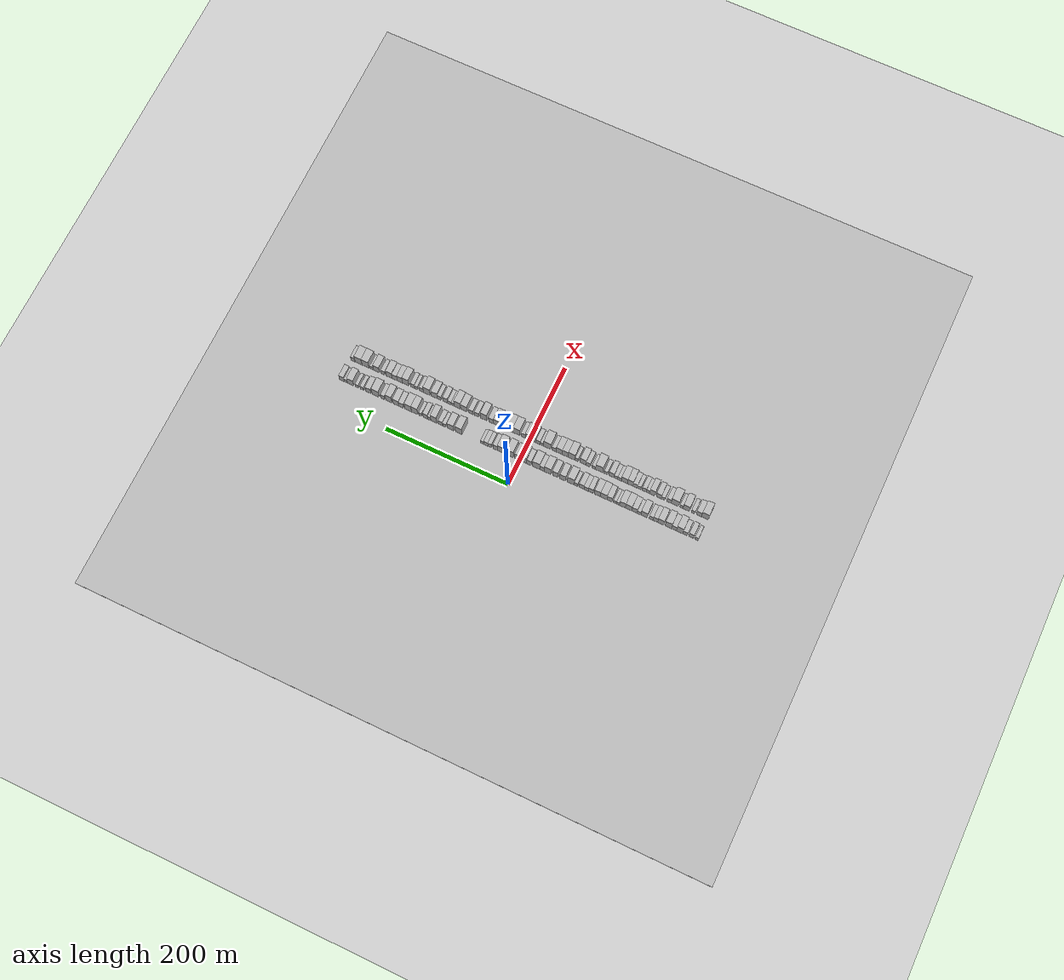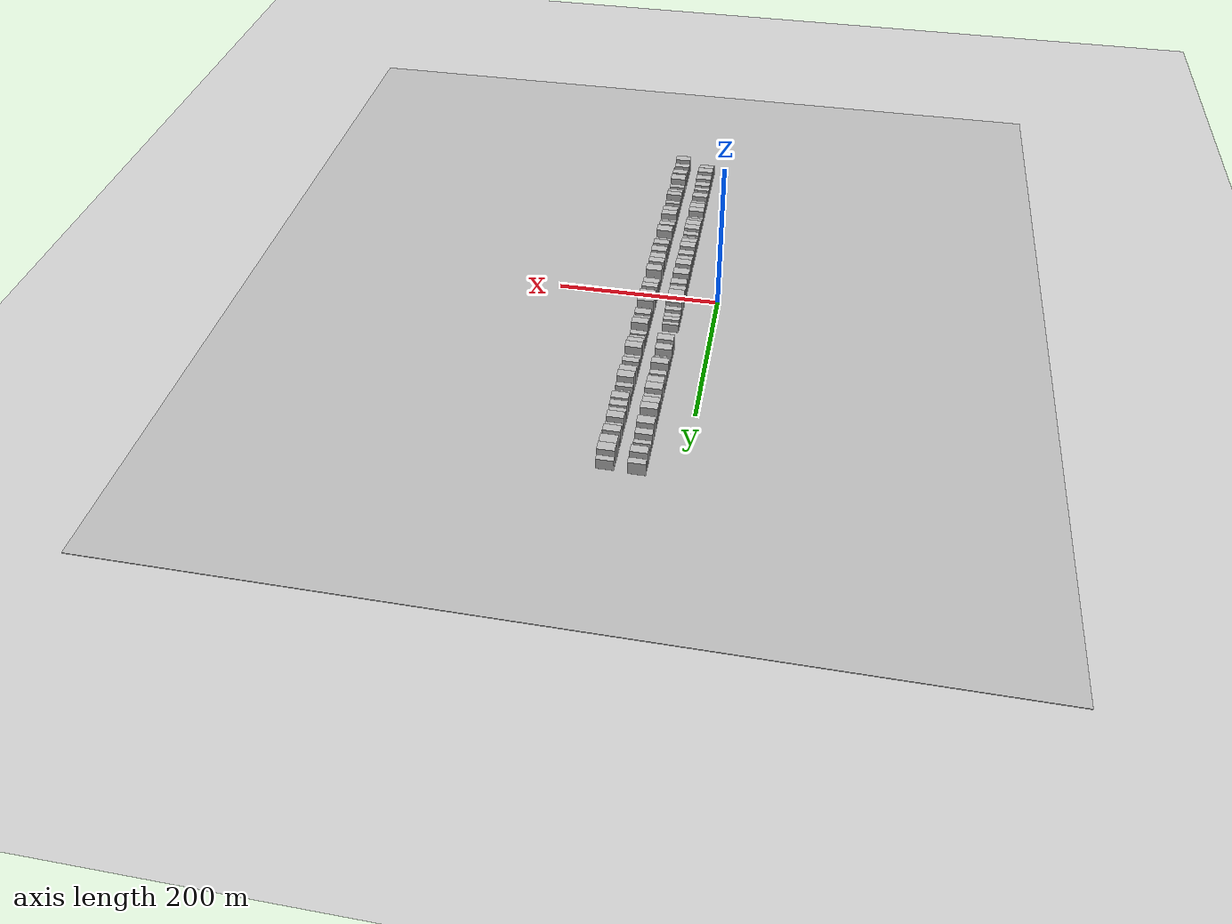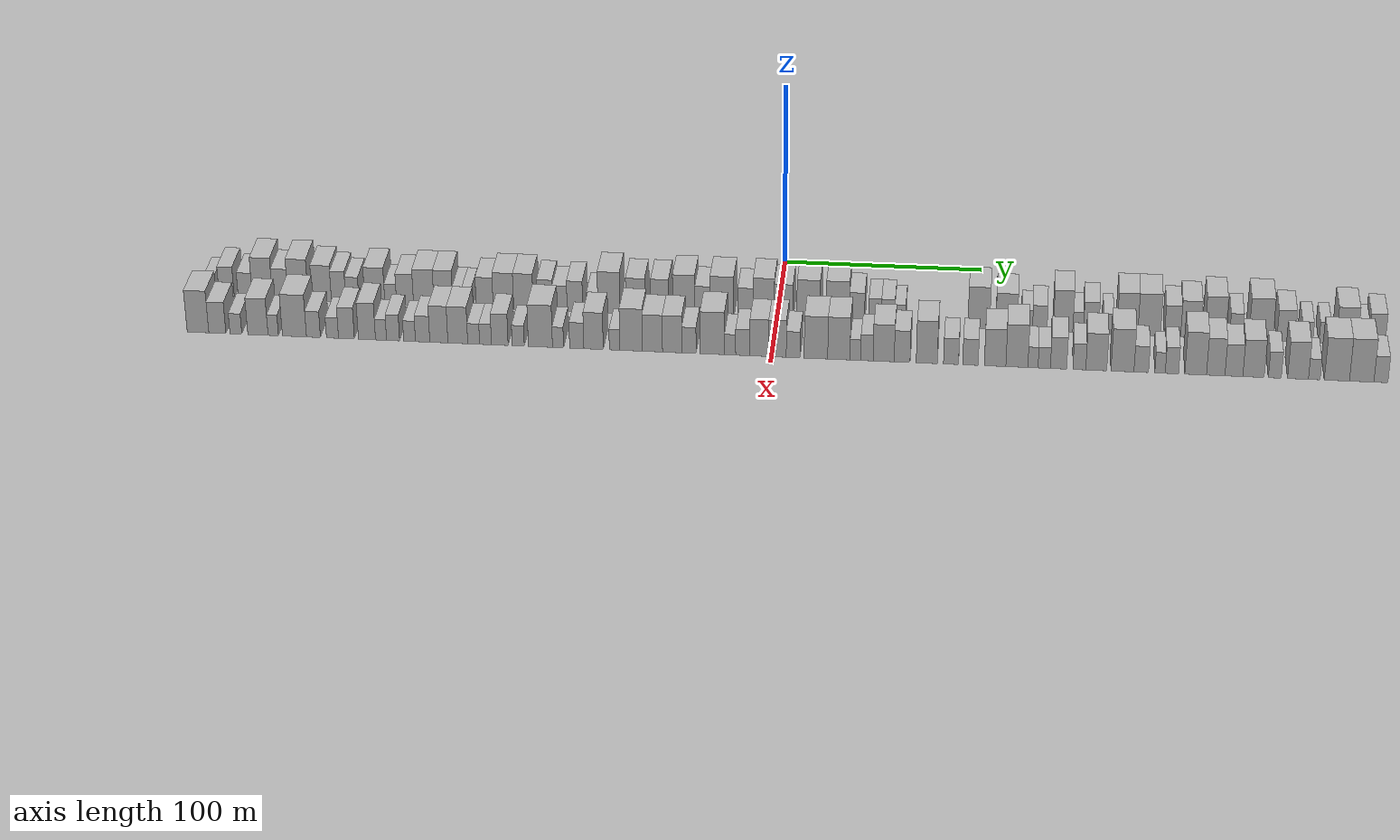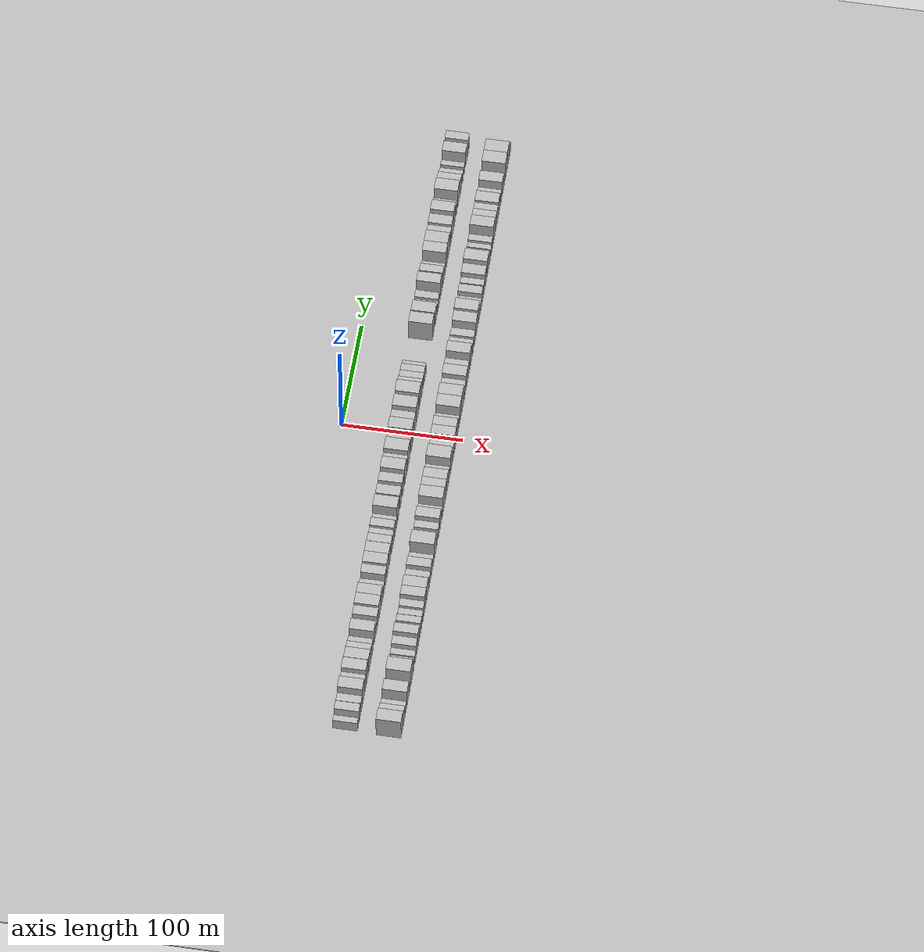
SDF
<?xml version="1.0" encoding="utf-8"?>

<sdf version="1.6">

   <world name="default">

      <gui fullscreen="0">

         <camera name="user_camera">

            <pose>-15 0 4.57585 0 0 0</pose>

            <view_controller>orbit</view_controller>

         </camera>

      </gui>

      <scene>

         <sky>

           <clouds>

             <speed>12</speed>

           </clouds>

         </sky>

         <ambient>0.4 0.4 0.4 1</ambient>

         <background>0.7 0.7 0.7 1</background>

         <shadows>1</shadows>

      </scene>

      <gravity>0 0 -9.8066</gravity>

      <magnetic_field>6e-06 2.3e-05 -4.2e-05</magnetic_field>

      <physics default="0" name="default_physics" type="ode">

         <ode>

            <solver>

               <type>quick</type>

               <iters>10</iters>

               <sor>1.0</sor>

               <use_dynamic_moi_rescaling>0</use_dynamic_moi_rescaling>

            </solver>

            <constraints>

               <cfm>0</cfm>

               <erp>0.2</erp>

               <contact_max_correcting_vel>100</contact_max_correcting_vel>

               <contact_surface_layer>0.001</contact_surface_layer>

            </constraints>

         </ode>

         <max_step_size>0.004</max_step_size>

         <real_time_factor>1</real_time_factor>

         <real_time_update_rate>250</real_time_update_rate>

      </physics>

      <light name="sun" type="directional">

         <cast_shadows>1</cast_shadows>

         <pose>0 0 10 0 0 0</pose>

         <diffuse>0.8 0.8 0.8 1</diffuse>

         <specular>0.2 0.2 0.2 1</specular>

         <attenuation>

            <range>1000</range>

            <constant>0.9</constant>

            <linear>0.01</linear>

            <quadratic>0.001</quadratic>

         </attenuation>

         <direction>-0.5 0.1 -0.9</direction>

      </light>

      <include>

         <name>ground_plane_1</name>

         <uri>model://HANNAS_ground_plane</uri>

         <pose>0 0 0  0 0 0</pose>

      </include>

      <include>

         <name>ground_plane_2</name>

         <uri>model://HANNAS_ground_plane</uri>

         <pose>100 0 0  0 0 0</pose>

      </include>

      <model name="building_1">

         <static>1</static>

         <pose frame="">50.0000 -284.3320 0 0.000000 0.000000 0.000000</pose>

         <link name="link">

            <pose frame="">0 0 6.00 0 0 0</pose>

            <collision name="collision">

               <geometry>

                  <box>

                     <size>20.0000 5.3359 12.0000</size>

                  </box>

               </geometry>

               <max_contacts>10</max_contacts>

               <surface>

                  <contact>

                     <ode/>

                  </contact>

                  <bounce/>

                  <friction>

                     <torsional>

                        <ode/>

                     </torsional>

                     <ode/>

                  </friction>

               </surface>

            </collision>

            <visual name="visual">

               <cast_shadows>0</cast_shadows>

               <geometry>

                  <box>

                     <size>20.0000 5.3359 12.0000</size>

                  </box>

               </geometry>

               <material>

                  <script>

                     <uri>model://HANNAS_wall/materials/scripts</uri>

                     <uri>model://HANNAS_wall/materials/textures</uri>

                     <name>vrc/HANNAS_wall</name>

                  </script>

               </material>

            </visual>

            <self_collide>0</self_collide>

            <enable_wind>0</enable_wind>

            <kinematic>0</kinematic>

         </link>

      </model>

      <model name="building_2">

         <static>1</static>

         <pose frame="">50.0000 -275.8561 0 0.000000 0.000000 0.000000</pose>

         <link name="link">

            <pose frame="">0 0 9.00 0 0 0</pose>

            <collision name="collision">

               <geometry>

                  <box>

                     <size>20.0000 7.6160 18.0000</size>

                  </box>

               </geometry>

               <max_contacts>10</max_contacts>

               <surface>

                  <contact>

                     <ode/>

                  </contact>

                  <bounce/>

                  <friction>

                     <torsional>

                        <ode/>

                     </torsional>

                     <ode/>

                  </friction>

               </surface>

            </collision>

            <visual name="visual">

               <cast_shadows>0</cast_shadows>

               <geometry>

                  <box>

                     <size>20.0000 7.6160 18.0000</size>

                  </box>

               </geometry>

               <material>

                  <script>

                     <uri>model://HANNAS_wall/materials/scripts</uri>

                     <uri>model://HANNAS_wall/materials/textures</uri>

                     <name>vrc/HANNAS_wall</name>

                  </script>

               </material>

            </visual>

            <self_collide>0</self_collide>

            <enable_wind>0</enable_wind>

            <kinematic>0</kinematic>

         </link>

      </model>

      <model name="building_3">

         <static>1</static>

         <pose frame="">50.0000 -266.4450 0 0.000000 0.000000 0.000000</pose>

         <link name="link">

            <pose frame="">0 0 7.50 0 0 0</pose>

            <collision name="collision">

               <geometry>

                  <box>

                     <size>20.0000 7.2062 15.0000</size>

                  </box>

               </geometry>

               <max_contacts>10</max_contacts>

               <surface>

                  <contact>

                     <ode/>

                  </contact>

                  <bounce/>

                  <friction>

                     <torsional>

                        <ode/>

                     </torsional>

                     <ode/>

                  </friction>

               </surface>

            </collision>

            <visual name="visual">

               <cast_shadows>0</cast_shadows>

               <geometry>

                  <box>

                     <size>20.0000 7.2062 15.0000</size>

                  </box>

               </geometry>

               <material>

                  <script>

                     <uri>model://HANNAS_wall/materials/scripts</uri>

                     <uri>model://HANNAS_wall/materials/textures</uri>

                     <name>vrc/HANNAS_wall</name>

                  </script>

               </material>

            </visual>

            <self_collide>0</self_collide>

            <enable_wind>0</enable_wind>

            <kinematic>0</kinematic>

         </link>

      </model>

      <model name="building_4">

         <static>1</static>

         <pose frame="">50.0000 -257.7383 0 0.000000 0.000000 0.000000</pose>

         <link name="link">

            <pose frame="">0 0 12.00 0 0 0</pose>

            <collision name="collision">

               <geometry>

                  <box>

                     <size>20.0000 10.2073 24.0000</size>

                  </box>

               </geometry>

               <max_contacts>10</max_contacts>

               <surface>

                  <contact>

                     <ode/>

                  </contact>

                  <bounce/>

                  <friction>

                     <torsional>

                        <ode/>

                     </torsional>

                     <ode/>

                  </friction>

               </surface>

            </collision>

            <visual name="visual">

               <cast_shadows>0</cast_shadows>

               <geometry>

                  <box>

                     <size>20.0000 10.2073 24.0000</size>

                  </box>

               </geometry>

               <material>

                  <script>

                     <uri>model://HANNAS_wall/materials/scripts</uri>

                     <uri>model://HANNAS_wall/materials/textures</uri>

                     <name>vrc/HANNAS_wall</name>

                  </script>

               </material>

            </visual>

            <self_collide>0</self_collide>

            <enable_wind>0</enable_wind>

            <kinematic>0</kinematic>

         </link>

      </model>

      <model name="building_5">

         <static>1</static>

         <pose frame="">50.0000 -248.7134 0 0.000000 0.000000 0.000000</pose>

         <link name="link">

            <pose frame="">0 0 9.00 0 0 0</pose>

            <collision name="collision">

               <geometry>

                  <box>

                     <size>20.0000 7.8425 18.0000</size>

                  </box>

               </geometry>

               <max_contacts>10</max_contacts>

               <surface>

                  <contact>

                     <ode/>

                  </contact>

                  <bounce/>

                  <friction>

                     <torsional>

                        <ode/>

                     </torsional>

                     <ode/>

                  </friction>

               </surface>

            </collision>

            <visual name="visual">

               <cast_shadows>0</cast_shadows>

               <geometry>

                  <box>

                     <size>20.0000 7.8425 18.0000</size>

                  </box>

               </geometry>

               <material>

                  <script>

                     <uri>model://HANNAS_wall/materials/scripts</uri>

                     <uri>model://HANNAS_wall/materials/textures</uri>

                     <name>vrc/HANNAS_wall</name>

                  </script>

               </material>

            </visual>

            <self_collide>0</self_collide>

            <enable_wind>0</enable_wind>

            <kinematic>0</kinematic>

         </link>

      </model>

      <model name="building_6">

         <static>1</static>

         <pose frame="">50.0000 -239.6760 0 0.000000 0.000000 0.000000</pose>

         <link name="link">

            <pose frame="">0 0 12.00 0 0 0</pose>

            <collision name="collision">

               <geometry>

                  <box>

                     <size>20.0000 10.2323 24.0000</size>

                  </box>

               </geometry>

               <max_contacts>10</max_contacts>

               <surface>

                  <contact>

                     <ode/>

                  </contact>

                  <bounce/>

                  <friction>

                     <torsional>

                        <ode/>

                     </torsional>

                     <ode/>

                  </friction>

               </surface>

            </collision>

            <visual name="visual">

               <cast_shadows>0</cast_shadows>

               <geometry>

                  <box>

                     <size>20.0000 10.2323 24.0000</size>

                  </box>

               </geometry>

               <material>

                  <script>

                     <uri>model://HANNAS_wall/materials/scripts</uri>

                     <uri>model://HANNAS_wall/materials/textures</uri>

                     <name>vrc/HANNAS_wall</name>

                  </script>

               </material>

            </visual>

            <self_collide>0</self_collide>

            <enable_wind>0</enable_wind>

            <kinematic>0</kinematic>

         </link>

      </model>

      <model name="building_7">

         <static>1</static>

         <pose frame="">50.0000 -227.7089 0 0.000000 0.000000 0.000000</pose>

         <link name="link">

            <pose frame="">0 0 10.50 0 0 0</pose>

            <collision name="collision">

               <geometry>

                  <box>

                     <size>20.0000 9.7018 21.0000</size>

                  </box>

               </geometry>

               <max_contacts>10</max_contacts>

               <surface>

                  <contact>

                     <ode/>

                  </contact>

                  <bounce/>

                  <friction>

                     <torsional>

                        <ode/>

                     </torsional>

                     <ode/>

                  </friction>

               </surface>

            </collision>

            <visual name="visual">

               <cast_shadows>0</cast_shadows>

               <geometry>

                  <box>

                     <size>20.0000 9.7018 21.0000</size>

                  </box>

               </geometry>

               <material>

                  <script>

                     <uri>model://HANNAS_wall/materials/scripts</uri>

                     <uri>model://HANNAS_wall/materials/textures</uri>

                     <name>vrc/HANNAS_wall</name>

                  </script>

               </material>

            </visual>

            <self_collide>0</self_collide>

            <enable_wind>0</enable_wind>

            <kinematic>0</kinematic>

         </link>

      </model>

      <model name="building_8">

         <static>1</static>

         <pose frame="">50.0000 -219.2189 0 0.000000 0.000000 0.000000</pose>

         <link name="link">

            <pose frame="">0 0 9.00 0 0 0</pose>

            <collision name="collision">

               <geometry>

                  <box>

                     <size>20.0000 7.2784 18.0000</size>

                  </box>

               </geometry>

               <max_contacts>10</max_contacts>

               <surface>

                  <contact>

                     <ode/>

                  </contact>

                  <bounce/>

                  <friction>

                     <torsional>

                        <ode/>

                     </torsional>

                     <ode/>

                  </friction>

               </surface>

            </collision>

            <visual name="visual">

               <cast_shadows>0</cast_shadows>

               <geometry>

                  <box>

                     <size>20.0000 7.2784 18.0000</size>

                  </box>

               </geometry>

               <material>

                  <script>

                     <uri>model://HANNAS_wall/materials/scripts</uri>

                     <uri>model://HANNAS_wall/materials/textures</uri>

                     <name>vrc/HANNAS_wall</name>

                  </script>

               </material>

            </visual>

            <self_collide>0</self_collide>

            <enable_wind>0</enable_wind>

            <kinematic>0</kinematic>

         </link>

      </model>

      <model name="building_9">

         <static>1</static>

         <pose frame="">50.0000 -212.2704 0 0.000000 0.000000 0.000000</pose>

         <link name="link">

            <pose frame="">0 0 7.50 0 0 0</pose>

            <collision name="collision">

               <geometry>

                  <box>

                     <size>20.0000 6.6184 15.0000</size>

                  </box>

               </geometry>

               <max_contacts>10</max_contacts>

               <surface>

                  <contact>

                     <ode/>

                  </contact>

                  <bounce/>

                  <friction>

                     <torsional>

                        <ode/>

                     </torsional>

                     <ode/>

                  </friction>

               </surface>

            </collision>

            <visual name="visual">

               <cast_shadows>0</cast_shadows>

               <geometry>

                  <box>

                     <size>20.0000 6.6184 15.0000</size>

                  </box>

               </geometry>

               <material>

                  <script>

                     <uri>model://HANNAS_wall/materials/scripts</uri>

                     <uri>model://HANNAS_wall/materials/textures</uri>

                     <name>vrc/HANNAS_wall</name>

                  </script>

               </material>

            </visual>

            <self_collide>0</self_collide>

            <enable_wind>0</enable_wind>

            <kinematic>0</kinematic>

         </link>

      </model>

      <model name="building_10">

         <static>1</static>

         <pose frame="">50.0000 -200.9258 0 0.000000 0.000000 0.000000</pose>

         <link name="link">

            <pose frame="">0 0 10.50 0 0 0</pose>

            <collision name="collision">

               <geometry>

                  <box>

                     <size>20.0000 10.0709 21.0000</size>

                  </box>

               </geometry>

               <max_contacts>10</max_contacts>

               <surface>

                  <contact>

                     <ode/>

                  </contact>

                  <bounce/>

                  <friction>

                     <torsional>

                        <ode/>

                     </torsional>

                     <ode/>

                  </friction>

               </surface>

            </collision>

            <visual name="visual">

               <cast_shadows>0</cast_shadows>

               <geometry>

                  <box>

                     <size>20.0000 10.0709 21.0000</size>

                  </box>

               </geometry>

               <material>

                  <script>

                     <uri>model://HANNAS_wall/materials/scripts</uri>

                     <uri>model://HANNAS_wall/materials/textures</uri>

                     <name>vrc/HANNAS_wall</name>

                  </script>

               </material>

            </visual>

            <self_collide>0</self_collide>

            <enable_wind>0</enable_wind>

            <kinematic>0</kinematic>

         </link>

      </model>

      <model name="building_11">

         <static>1</static>

         <pose frame="">50.0000 -192.9457 0 0.000000 0.000000 0.000000</pose>

         <link name="link">

            <pose frame="">0 0 6.00 0 0 0</pose>

            <collision name="collision">

               <geometry>

                  <box>

                     <size>20.0000 5.8891 12.0000</size>

                  </box>

               </geometry>

               <max_contacts>10</max_contacts>

               <surface>

                  <contact>

                     <ode/>

                  </contact>

                  <bounce/>

                  <friction>

                     <torsional>

                        <ode/>

                     </torsional>

                     <ode/>

                  </friction>

               </surface>

            </collision>

            <visual name="visual">

               <cast_shadows>0</cast_shadows>

               <geometry>

                  <box>

                     <size>20.0000 5.8891 12.0000</size>

                  </box>

               </geometry>

               <material>

                  <script>

                     <uri>model://HANNAS_wall/materials/scripts</uri>

                     <uri>model://HANNAS_wall/materials/textures</uri>

                     <name>vrc/HANNAS_wall</name>

                  </script>

               </material>

            </visual>

            <self_collide>0</self_collide>

            <enable_wind>0</enable_wind>

            <kinematic>0</kinematic>

         </link>

      </model>

      <model name="building_12">

         <static>1</static>

         <pose frame="">50.0000 -185.7282 0 0.000000 0.000000 0.000000</pose>

         <link name="link">

            <pose frame="">0 0 9.00 0 0 0</pose>

            <collision name="collision">

               <geometry>

                  <box>

                     <size>20.0000 8.5458 18.0000</size>

                  </box>

               </geometry>

               <max_contacts>10</max_contacts>

               <surface>

                  <contact>

                     <ode/>

                  </contact>

                  <bounce/>

                  <friction>

                     <torsional>

                        <ode/>

                     </torsional>

                     <ode/>

                  </friction>

               </surface>

            </collision>

            <visual name="visual">

               <cast_shadows>0</cast_shadows>

               <geometry>

                  <box>

                     <size>20.0000 8.5458 18.0000</size>

                  </box>

               </geometry>

               <material>

                  <script>

                     <uri>model://HANNAS_wall/materials/scripts</uri>

                     <uri>model://HANNAS_wall/materials/textures</uri>

                     <name>vrc/HANNAS_wall</name>

                  </script>

               </material>

            </visual>

            <self_collide>0</self_collide>

            <enable_wind>0</enable_wind>

            <kinematic>0</kinematic>

         </link>

      </model>

      <model name="building_13">

         <static>1</static>

         <pose frame="">50.0000 -176.3089 0 0.000000 0.000000 0.000000</pose>

         <link name="link">

            <pose frame="">0 0 10.50 0 0 0</pose>

            <collision name="collision">

               <geometry>

                  <box>

                     <size>20.0000 10.2928 21.0000</size>

                  </box>

               </geometry>

               <max_contacts>10</max_contacts>

               <surface>

                  <contact>

                     <ode/>

                  </contact>

                  <bounce/>

                  <friction>

                     <torsional>

                        <ode/>

                     </torsional>

                     <ode/>

                  </friction>

               </surface>

            </collision>

            <visual name="visual">

               <cast_shadows>0</cast_shadows>

               <geometry>

                  <box>

                     <size>20.0000 10.2928 21.0000</size>

                  </box>

               </geometry>

               <material>

                  <script>

                     <uri>model://HANNAS_wall/materials/scripts</uri>

                     <uri>model://HANNAS_wall/materials/textures</uri>

                     <name>vrc/HANNAS_wall</name>

                  </script>

               </material>

            </visual>

            <self_collide>0</self_collide>

            <enable_wind>0</enable_wind>

            <kinematic>0</kinematic>

         </link>

      </model>

      <model name="building_14">

         <static>1</static>

         <pose frame="">50.0000 -166.4119 0 0.000000 0.000000 0.000000</pose>

         <link name="link">

            <pose frame="">0 0 10.50 0 0 0</pose>

            <collision name="collision">

               <geometry>

                  <box>

                     <size>20.0000 9.5012 21.0000</size>

                  </box>

               </geometry>

               <max_contacts>10</max_contacts>

               <surface>

                  <contact>

                     <ode/>

                  </contact>

                  <bounce/>

                  <friction>

                     <torsional>

                        <ode/>

                     </torsional>

                     <ode/>

                  </friction>

               </surface>

            </collision>

            <visual name="visual">

               <cast_shadows>0</cast_shadows>

               <geometry>

                  <box>

                     <size>20.0000 9.5012 21.0000</size>

                  </box>

               </geometry>

               <material>

                  <script>

                     <uri>model://HANNAS_wall/materials/scripts</uri>

                     <uri>model://HANNAS_wall/materials/textures</uri>

                     <name>vrc/HANNAS_wall</name>

                  </script>

               </material>

            </visual>

            <self_collide>0</self_collide>

            <enable_wind>0</enable_wind>

            <kinematic>0</kinematic>

         </link>

      </model>

      <model name="building_15">

         <static>1</static>

         <pose frame="">50.0000 -159.2189 0 0.000000 0.000000 0.000000</pose>

         <link name="link">

            <pose frame="">0 0 6.00 0 0 0</pose>

            <collision name="collision">

               <geometry>

                  <box>

                     <size>20.0000 4.8848 12.0000</size>

                  </box>

               </geometry>

               <max_contacts>10</max_contacts>

               <surface>

                  <contact>

                     <ode/>

                  </contact>

                  <bounce/>

                  <friction>

                     <torsional>

                        <ode/>

                     </torsional>

                     <ode/>

                  </friction>

               </surface>

            </collision>

            <visual name="visual">

               <cast_shadows>0</cast_shadows>

               <geometry>

                  <box>

                     <size>20.0000 4.8848 12.0000</size>

                  </box>

               </geometry>

               <material>

                  <script>

                     <uri>model://HANNAS_wall/materials/scripts</uri>

                     <uri>model://HANNAS_wall/materials/textures</uri>

                     <name>vrc/HANNAS_wall</name>

                  </script>

               </material>

            </visual>

            <self_collide>0</self_collide>

            <enable_wind>0</enable_wind>

            <kinematic>0</kinematic>

         </link>

      </model>

      <model name="building_16">

         <static>1</static>

         <pose frame="">50.0000 -154.3433 0 0.000000 0.000000 0.000000</pose>

         <link name="link">

            <pose frame="">0 0 6.00 0 0 0</pose>

            <collision name="collision">

               <geometry>

                  <box>

                     <size>20.0000 4.8665 12.0000</size>

                  </box>

               </geometry>

               <max_contacts>10</max_contacts>

               <surface>

                  <contact>

                     <ode/>

                  </contact>

                  <bounce/>

                  <friction>

                     <torsional>

                        <ode/>

                     </torsional>

                     <ode/>

                  </friction>

               </surface>

            </collision>

            <visual name="visual">

               <cast_shadows>0</cast_shadows>

               <geometry>

                  <box>

                     <size>20.0000 4.8665 12.0000</size>

                  </box>

               </geometry>

               <material>

                  <script>

                     <uri>model://HANNAS_wall/materials/scripts</uri>

                     <uri>model://HANNAS_wall/materials/textures</uri>

                     <name>vrc/HANNAS_wall</name>

                  </script>

               </material>

            </visual>

            <self_collide>0</self_collide>

            <enable_wind>0</enable_wind>

            <kinematic>0</kinematic>

         </link>

      </model>

      <model name="building_17">

         <static>1</static>

         <pose frame="">50.0000 -145.6713 0 0.000000 0.000000 0.000000</pose>

         <link name="link">

            <pose frame="">0 0 9.00 0 0 0</pose>

            <collision name="collision">

               <geometry>

                  <box>

                     <size>20.0000 8.4777 18.0000</size>

                  </box>

               </geometry>

               <max_contacts>10</max_contacts>

               <surface>

                  <contact>

                     <ode/>

                  </contact>

                  <bounce/>

                  <friction>

                     <torsional>

                        <ode/>

                     </torsional>

                     <ode/>

                  </friction>

               </surface>

            </collision>

            <visual name="visual">

               <cast_shadows>0</cast_shadows>

               <geometry>

                  <box>

                     <size>20.0000 8.4777 18.0000</size>

                  </box>

               </geometry>

               <material>

                  <script>

                     <uri>model://HANNAS_wall/materials/scripts</uri>

                     <uri>model://HANNAS_wall/materials/textures</uri>

                     <name>vrc/HANNAS_wall</name>

                  </script>

               </material>

            </visual>

            <self_collide>0</self_collide>

            <enable_wind>0</enable_wind>

            <kinematic>0</kinematic>

         </link>

      </model>

      <model name="building_18">

         <static>1</static>

         <pose frame="">50.0000 -136.2820 0 0.000000 0.000000 0.000000</pose>

         <link name="link">

            <pose frame="">0 0 10.50 0 0 0</pose>

            <collision name="collision">

               <geometry>

                  <box>

                     <size>20.0000 10.3009 21.0000</size>

                  </box>

               </geometry>

               <max_contacts>10</max_contacts>

               <surface>

                  <contact>

                     <ode/>

                  </contact>

                  <bounce/>

                  <friction>

                     <torsional>

                        <ode/>

                     </torsional>

                     <ode/>

                  </friction>

               </surface>

            </collision>

            <visual name="visual">

               <cast_shadows>0</cast_shadows>

               <geometry>

                  <box>

                     <size>20.0000 10.3009 21.0000</size>

                  </box>

               </geometry>

               <material>

                  <script>

                     <uri>model://HANNAS_wall/materials/scripts</uri>

                     <uri>model://HANNAS_wall/materials/textures</uri>

                     <name>vrc/HANNAS_wall</name>

                  </script>

               </material>

            </visual>

            <self_collide>0</self_collide>

            <enable_wind>0</enable_wind>

            <kinematic>0</kinematic>

         </link>

      </model>

      <model name="building_19">

         <static>1</static>

         <pose frame="">50.0000 -126.2274 0 0.000000 0.000000 0.000000</pose>

         <link name="link">

            <pose frame="">0 0 10.50 0 0 0</pose>

            <collision name="collision">

               <geometry>

                  <box>

                     <size>20.0000 9.8082 21.0000</size>

                  </box>

               </geometry>

               <max_contacts>10</max_contacts>

               <surface>

                  <contact>

                     <ode/>

                  </contact>

                  <bounce/>

                  <friction>

                     <torsional>

                        <ode/>

                     </torsional>

                     <ode/>

                  </friction>

               </surface>

            </collision>

            <visual name="visual">

               <cast_shadows>0</cast_shadows>

               <geometry>

                  <box>

                     <size>20.0000 9.8082 21.0000</size>

                  </box>

               </geometry>

               <material>

                  <script>

                     <uri>model://HANNAS_wall/materials/scripts</uri>

                     <uri>model://HANNAS_wall/materials/textures</uri>

                     <name>vrc/HANNAS_wall</name>

                  </script>

               </material>

            </visual>

            <self_collide>0</self_collide>

            <enable_wind>0</enable_wind>

            <kinematic>0</kinematic>

         </link>

      </model>

      <model name="building_20">

         <static>1</static>

         <pose frame="">50.0000 -115.4698 0 0.000000 0.000000 0.000000</pose>

         <link name="link">

            <pose frame="">0 0 9.00 0 0 0</pose>

            <collision name="collision">

               <geometry>

                  <box>

                     <size>20.0000 7.7070 18.0000</size>

                  </box>

               </geometry>

               <max_contacts>10</max_contacts>

               <surface>

                  <contact>

                     <ode/>

                  </contact>

                  <bounce/>

                  <friction>

                     <torsional>

                        <ode/>

                     </torsional>

                     <ode/>

                  </friction>

               </surface>

            </collision>

            <visual name="visual">

               <cast_shadows>0</cast_shadows>

               <geometry>

                  <box>

                     <size>20.0000 7.7070 18.0000</size>

                  </box>

               </geometry>

               <material>

                  <script>

                     <uri>model://HANNAS_wall/materials/scripts</uri>

                     <uri>model://HANNAS_wall/materials/textures</uri>

                     <name>vrc/HANNAS_wall</name>

                  </script>

               </material>

            </visual>

            <self_collide>0</self_collide>

            <enable_wind>0</enable_wind>

            <kinematic>0</kinematic>

         </link>

      </model>

      <model name="building_21">

         <static>1</static>

         <pose frame="">50.0000 -107.9874 0 0.000000 0.000000 0.000000</pose>

         <link name="link">

            <pose frame="">0 0 7.50 0 0 0</pose>

            <collision name="collision">

               <geometry>

                  <box>

                     <size>20.0000 7.2578 15.0000</size>

                  </box>

               </geometry>

               <max_contacts>10</max_contacts>

               <surface>

                  <contact>

                     <ode/>

                  </contact>

                  <bounce/>

                  <friction>

                     <torsional>

                        <ode/>

                     </torsional>

                     <ode/>

                  </friction>

               </surface>

            </collision>

            <visual name="visual">

               <cast_shadows>0</cast_shadows>

               <geometry>

                  <box>

                     <size>20.0000 7.2578 15.0000</size>

                  </box>

               </geometry>

               <material>

                  <script>

                     <uri>model://HANNAS_wall/materials/scripts</uri>

                     <uri>model://HANNAS_wall/materials/textures</uri>

                     <name>vrc/HANNAS_wall</name>

                  </script>

               </material>

            </visual>

            <self_collide>0</self_collide>

            <enable_wind>0</enable_wind>

            <kinematic>0</kinematic>

         </link>

      </model>

      <model name="building_22">

         <static>1</static>

         <pose frame="">50.0000 -100.4647 0 0.000000 0.000000 0.000000</pose>

         <link name="link">

            <pose frame="">0 0 9.00 0 0 0</pose>

            <collision name="collision">

               <geometry>

                  <box>

                     <size>20.0000 7.7876 18.0000</size>

                  </box>

               </geometry>

               <max_contacts>10</max_contacts>

               <surface>

                  <contact>

                     <ode/>

                  </contact>

                  <bounce/>

                  <friction>

                     <torsional>

                        <ode/>

                     </torsional>

                     <ode/>

                  </friction>

               </surface>

            </collision>

            <visual name="visual">

               <cast_shadows>0</cast_shadows>

               <geometry>

                  <box>

                     <size>20.0000 7.7876 18.0000</size>

                  </box>

               </geometry>

               <material>

                  <script>

                     <uri>model://HANNAS_wall/materials/scripts</uri>

                     <uri>model://HANNAS_wall/materials/textures</uri>

                     <name>vrc/HANNAS_wall</name>

                  </script>

               </material>

            </visual>

            <self_collide>0</self_collide>

            <enable_wind>0</enable_wind>

            <kinematic>0</kinematic>

         </link>

      </model>

      <model name="building_23">

         <static>1</static>

         <pose frame="">50.0000 -91.7634 0 0.000000 0.000000 0.000000</pose>

         <link name="link">

            <pose frame="">0 0 6.00 0 0 0</pose>

            <collision name="collision">

               <geometry>

                  <box>

                     <size>20.0000 5.6151 12.0000</size>

                  </box>

               </geometry>

               <max_contacts>10</max_contacts>

               <surface>

                  <contact>

                     <ode/>

                  </contact>

                  <bounce/>

                  <friction>

                     <torsional>

                        <ode/>

                     </torsional>

                     <ode/>

                  </friction>

               </surface>

            </collision>

            <visual name="visual">

               <cast_shadows>0</cast_shadows>

               <geometry>

                  <box>

                     <size>20.0000 5.6151 12.0000</size>

                  </box>

               </geometry>

               <material>

                  <script>

                     <uri>model://HANNAS_wall/materials/scripts</uri>

                     <uri>model://HANNAS_wall/materials/textures</uri>

                     <name>vrc/HANNAS_wall</name>

                  </script>

               </material>

            </visual>

            <self_collide>0</self_collide>

            <enable_wind>0</enable_wind>

            <kinematic>0</kinematic>

         </link>

      </model>

      <model name="building_24">

         <static>1</static>

         <pose frame="">50.0000 -83.4513 0 0.000000 0.000000 0.000000</pose>

         <link name="link">

            <pose frame="">0 0 12.00 0 0 0</pose>

            <collision name="collision">

               <geometry>

                  <box>

                     <size>20.0000 11.0090 24.0000</size>

                  </box>

               </geometry>

               <max_contacts>10</max_contacts>

               <surface>

                  <contact>

                     <ode/>

                  </contact>

                  <bounce/>

                  <friction>

                     <torsional>

                        <ode/>

                     </torsional>

                     <ode/>

                  </friction>

               </surface>

            </collision>

            <visual name="visual">

               <cast_shadows>0</cast_shadows>

               <geometry>

                  <box>

                     <size>20.0000 11.0090 24.0000</size>

                  </box>

               </geometry>

               <material>

                  <script>

                     <uri>model://HANNAS_wall/materials/scripts</uri>

                     <uri>model://HANNAS_wall/materials/textures</uri>

                     <name>vrc/HANNAS_wall</name>

                  </script>

               </material>

            </visual>

            <self_collide>0</self_collide>

            <enable_wind>0</enable_wind>

            <kinematic>0</kinematic>

         </link>

      </model>

      <model name="building_25">

         <static>1</static>

         <pose frame="">50.0000 -70.2266 0 0.000000 0.000000 0.000000</pose>

         <link name="link">

            <pose frame="">0 0 10.50 0 0 0</pose>

            <collision name="collision">

               <geometry>

                  <box>

                     <size>20.0000 9.4404 21.0000</size>

                  </box>

               </geometry>

               <max_contacts>10</max_contacts>

               <surface>

                  <contact>

                     <ode/>

                  </contact>

                  <bounce/>

                  <friction>

                     <torsional>

                        <ode/>

                     </torsional>

                     <ode/>

                  </friction>

               </surface>

            </collision>

            <visual name="visual">

               <cast_shadows>0</cast_shadows>

               <geometry>

                  <box>

                     <size>20.0000 9.4404 21.0000</size>

                  </box>

               </geometry>

               <material>

                  <script>

                     <uri>model://HANNAS_wall/materials/scripts</uri>

                     <uri>model://HANNAS_wall/materials/textures</uri>

                     <name>vrc/HANNAS_wall</name>

                  </script>

               </material>

            </visual>

            <self_collide>0</self_collide>

            <enable_wind>0</enable_wind>

            <kinematic>0</kinematic>

         </link>

      </model>

      <model name="building_26">

         <static>1</static>

         <pose frame="">50.0000 -58.0610 0 0.000000 0.000000 0.000000</pose>

         <link name="link">

            <pose frame="">0 0 10.50 0 0 0</pose>

            <collision name="collision">

               <geometry>

                  <box>

                     <size>20.0000 8.8907 21.0000</size>

                  </box>

               </geometry>

               <max_contacts>10</max_contacts>

               <surface>

                  <contact>

                     <ode/>

                  </contact>

                  <bounce/>

                  <friction>

                     <torsional>

                        <ode/>

                     </torsional>

                     <ode/>

                  </friction>

               </surface>

            </collision>

            <visual name="visual">

               <cast_shadows>0</cast_shadows>

               <geometry>

                  <box>

                     <size>20.0000 8.8907 21.0000</size>

                  </box>

               </geometry>

               <material>

                  <script>

                     <uri>model://HANNAS_wall/materials/scripts</uri>

                     <uri>model://HANNAS_wall/materials/textures</uri>

                     <name>vrc/HANNAS_wall</name>

                  </script>

               </material>

            </visual>

            <self_collide>0</self_collide>

            <enable_wind>0</enable_wind>

            <kinematic>0</kinematic>

         </link>

      </model>

      <model name="building_27">

         <static>1</static>

         <pose frame="">50.0000 -46.1126 0 0.000000 0.000000 0.000000</pose>

         <link name="link">

            <pose frame="">0 0 12.00 0 0 0</pose>

            <collision name="collision">

               <geometry>

                  <box>

                     <size>20.0000 11.0061 24.0000</size>

                  </box>

               </geometry>

               <max_contacts>10</max_contacts>

               <surface>

                  <contact>

                     <ode/>

                  </contact>

                  <bounce/>

                  <friction>

                     <torsional>

                        <ode/>

                     </torsional>

                     <ode/>

                  </friction>

               </surface>

            </collision>

            <visual name="visual">

               <cast_shadows>0</cast_shadows>

               <geometry>

                  <box>

                     <size>20.0000 11.0061 24.0000</size>

                  </box>

               </geometry>

               <material>

                  <script>

                     <uri>model://HANNAS_wall/materials/scripts</uri>

                     <uri>model://HANNAS_wall/materials/textures</uri>

                     <name>vrc/HANNAS_wall</name>

                  </script>

               </material>

            </visual>

            <self_collide>0</self_collide>

            <enable_wind>0</enable_wind>

            <kinematic>0</kinematic>

         </link>

      </model>

      <model name="building_28">

         <static>1</static>

         <pose frame="">50.0000 -36.8444 0 0.000000 0.000000 0.000000</pose>

         <link name="link">

            <pose frame="">0 0 9.00 0 0 0</pose>

            <collision name="collision">

               <geometry>

                  <box>

                     <size>20.0000 7.5302 18.0000</size>

                  </box>

               </geometry>

               <max_contacts>10</max_contacts>

               <surface>

                  <contact>

                     <ode/>

                  </contact>

                  <bounce/>

                  <friction>

                     <torsional>

                        <ode/>

                     </torsional>

                     <ode/>

                  </friction>

               </surface>

            </collision>

            <visual name="visual">

               <cast_shadows>0</cast_shadows>

               <geometry>

                  <box>

                     <size>20.0000 7.5302 18.0000</size>

                  </box>

               </geometry>

               <material>

                  <script>

                     <uri>model://HANNAS_wall/materials/scripts</uri>

                     <uri>model://HANNAS_wall/materials/textures</uri>

                     <name>vrc/HANNAS_wall</name>

                  </script>

               </material>

            </visual>

            <self_collide>0</self_collide>

            <enable_wind>0</enable_wind>

            <kinematic>0</kinematic>

         </link>

      </model>

      <model name="building_29">

         <static>1</static>

         <pose frame="">50.0000 -27.2090 0 0.000000 0.000000 0.000000</pose>

         <link name="link">

            <pose frame="">0 0 12.00 0 0 0</pose>

            <collision name="collision">

               <geometry>

                  <box>

                     <size>20.0000 11.7405 24.0000</size>

                  </box>

               </geometry>

               <max_contacts>10</max_contacts>

               <surface>

                  <contact>

                     <ode/>

                  </contact>

                  <bounce/>

                  <friction>

                     <torsional>

                        <ode/>

                     </torsional>

                     <ode/>

                  </friction>

               </surface>

            </collision>

            <visual name="visual">

               <cast_shadows>0</cast_shadows>

               <geometry>

                  <box>

                     <size>20.0000 11.7405 24.0000</size>

                  </box>

               </geometry>

               <material>

                  <script>

                     <uri>model://HANNAS_wall/materials/scripts</uri>

                     <uri>model://HANNAS_wall/materials/textures</uri>

                     <name>vrc/HANNAS_wall</name>

                  </script>

               </material>

            </visual>

            <self_collide>0</self_collide>

            <enable_wind>0</enable_wind>

            <kinematic>0</kinematic>

         </link>

      </model>

      <model name="building_30">

         <static>1</static>

         <pose frame="">50.0000 -15.5463 0 0.000000 0.000000 0.000000</pose>

         <link name="link">

            <pose frame="">0 0 9.00 0 0 0</pose>

            <collision name="collision">

               <geometry>

                  <box>

                     <size>20.0000 7.5850 18.0000</size>

                  </box>

               </geometry>

               <max_contacts>10</max_contacts>

               <surface>

                  <contact>

                     <ode/>

                  </contact>

                  <bounce/>

                  <friction>

                     <torsional>

                        <ode/>

                     </torsional>

                     <ode/>

                  </friction>

               </surface>

            </collision>

            <visual name="visual">

               <cast_shadows>0</cast_shadows>

               <geometry>

                  <box>

                     <size>20.0000 7.5850 18.0000</size>

                  </box>

               </geometry>

               <material>

                  <script>

                     <uri>model://HANNAS_wall/materials/scripts</uri>

                     <uri>model://HANNAS_wall/materials/textures</uri>

                     <name>vrc/HANNAS_wall</name>

                  </script>

               </material>

            </visual>

            <self_collide>0</self_collide>

            <enable_wind>0</enable_wind>

            <kinematic>0</kinematic>

         </link>

      </model>

      <model name="building_31">

         <static>1</static>

         <pose frame="">50.0000 -6.4729 0 0.000000 0.000000 0.000000</pose>

         <link name="link">

            <pose frame="">0 0 12.00 0 0 0</pose>

            <collision name="collision">

               <geometry>

                  <box>

                     <size>20.0000 10.5618 24.0000</size>

                  </box>

               </geometry>

               <max_contacts>10</max_contacts>

               <surface>

                  <contact>

                     <ode/>

                  </contact>

                  <bounce/>

                  <friction>

                     <torsional>

                        <ode/>

                     </torsional>

                     <ode/>

                  </friction>

               </surface>

            </collision>

            <visual name="visual">

               <cast_shadows>0</cast_shadows>

               <geometry>

                  <box>

                     <size>20.0000 10.5618 24.0000</size>

                  </box>

               </geometry>

               <material>

                  <script>

                     <uri>model://HANNAS_wall/materials/scripts</uri>

                     <uri>model://HANNAS_wall/materials/textures</uri>

                     <name>vrc/HANNAS_wall</name>

                  </script>

               </material>

            </visual>

            <self_collide>0</self_collide>

            <enable_wind>0</enable_wind>

            <kinematic>0</kinematic>

         </link>

      </model>

      <model name="building_32">

         <static>1</static>

         <pose frame="">50.0000 3.3889 0 0.000000 0.000000 0.000000</pose>

         <link name="link">

            <pose frame="">0 0 10.50 0 0 0</pose>

            <collision name="collision">

               <geometry>

                  <box>

                     <size>20.0000 9.1619 21.0000</size>

                  </box>

               </geometry>

               <max_contacts>10</max_contacts>

               <surface>

                  <contact>

                     <ode/>

                  </contact>

                  <bounce/>

                  <friction>

                     <torsional>

                        <ode/>

                     </torsional>

                     <ode/>

                  </friction>

               </surface>

            </collision>

            <visual name="visual">

               <cast_shadows>0</cast_shadows>

               <geometry>

                  <box>

                     <size>20.0000 9.1619 21.0000</size>

                  </box>

               </geometry>

               <material>

                  <script>

                     <uri>model://HANNAS_wall/materials/scripts</uri>

                     <uri>model://HANNAS_wall/materials/textures</uri>

                     <name>vrc/HANNAS_wall</name>

                  </script>

               </material>

            </visual>

            <self_collide>0</self_collide>

            <enable_wind>0</enable_wind>

            <kinematic>0</kinematic>

         </link>

      </model>

      <model name="building_33">

         <static>1</static>

         <pose frame="">50.0000 15.7041 0 0.000000 0.000000 0.000000</pose>

         <link name="link">

            <pose frame="">0 0 12.00 0 0 0</pose>

            <collision name="collision">

               <geometry>

                  <box>

                     <size>20.0000 11.4685 24.0000</size>

                  </box>

               </geometry>

               <max_contacts>10</max_contacts>

               <surface>

                  <contact>

                     <ode/>

                  </contact>

                  <bounce/>

                  <friction>

                     <torsional>

                        <ode/>

                     </torsional>

                     <ode/>

                  </friction>

               </surface>

            </collision>

            <visual name="visual">

               <cast_shadows>0</cast_shadows>

               <geometry>

                  <box>

                     <size>20.0000 11.4685 24.0000</size>

                  </box>

               </geometry>

               <material>

                  <script>

                     <uri>model://HANNAS_wall/materials/scripts</uri>

                     <uri>model://HANNAS_wall/materials/textures</uri>

                     <name>vrc/HANNAS_wall</name>

                  </script>

               </material>

            </visual>

            <self_collide>0</self_collide>

            <enable_wind>0</enable_wind>

            <kinematic>0</kinematic>

         </link>

      </model>

      <model name="building_34">

         <static>1</static>

         <pose frame="">50.0000 30.1727 0 0.000000 0.000000 0.000000</pose>

         <link name="link">

            <pose frame="">0 0 12.00 0 0 0</pose>

            <collision name="collision">

               <geometry>

                  <box>

                     <size>20.0000 11.4687 24.0000</size>

                  </box>

               </geometry>

               <max_contacts>10</max_contacts>

               <surface>

                  <contact>

                     <ode/>

                  </contact>

                  <bounce/>

                  <friction>

                     <torsional>

                        <ode/>

                     </torsional>

                     <ode/>

                  </friction>

               </surface>

            </collision>

            <visual name="visual">

               <cast_shadows>0</cast_shadows>

               <geometry>

                  <box>

                     <size>20.0000 11.4687 24.0000</size>

                  </box>

               </geometry>

               <material>

                  <script>

                     <uri>model://HANNAS_wall/materials/scripts</uri>

                     <uri>model://HANNAS_wall/materials/textures</uri>

                     <name>vrc/HANNAS_wall</name>

                  </script>

               </material>

            </visual>

            <self_collide>0</self_collide>

            <enable_wind>0</enable_wind>

            <kinematic>0</kinematic>

         </link>

      </model>

      <model name="building_35">

         <static>1</static>

         <pose frame="">50.0000 39.6602 0 0.000000 0.000000 0.000000</pose>

         <link name="link">

            <pose frame="">0 0 9.00 0 0 0</pose>

            <collision name="collision">

               <geometry>

                  <box>

                     <size>20.0000 7.5063 18.0000</size>

                  </box>

               </geometry>

               <max_contacts>10</max_contacts>

               <surface>

                  <contact>

                     <ode/>

                  </contact>

                  <bounce/>

                  <friction>

                     <torsional>

                        <ode/>

                     </torsional>

                     <ode/>

                  </friction>

               </surface>

            </collision>

            <visual name="visual">

               <cast_shadows>0</cast_shadows>

               <geometry>

                  <box>

                     <size>20.0000 7.5063 18.0000</size>

                  </box>

               </geometry>

               <material>

                  <script>

                     <uri>model://HANNAS_wall/materials/scripts</uri>

                     <uri>model://HANNAS_wall/materials/textures</uri>

                     <name>vrc/HANNAS_wall</name>

                  </script>

               </material>

            </visual>

            <self_collide>0</self_collide>

            <enable_wind>0</enable_wind>

            <kinematic>0</kinematic>

         </link>

      </model>

      <model name="building_36">

         <static>1</static>

         <pose frame="">50.0000 48.5422 0 0.000000 0.000000 0.000000</pose>

         <link name="link">

            <pose frame="">0 0 7.50 0 0 0</pose>

            <collision name="collision">

               <geometry>

                  <box>

                     <size>20.0000 6.2576 15.0000</size>

                  </box>

               </geometry>

               <max_contacts>10</max_contacts>

               <surface>

                  <contact>

                     <ode/>

                  </contact>

                  <bounce/>

                  <friction>

                     <torsional>

                        <ode/>

                     </torsional>

                     <ode/>

                  </friction>

               </surface>

            </collision>

            <visual name="visual">

               <cast_shadows>0</cast_shadows>

               <geometry>

                  <box>

                     <size>20.0000 6.2576 15.0000</size>

                  </box>

               </geometry>

               <material>

                  <script>

                     <uri>model://HANNAS_wall/materials/scripts</uri>

                     <uri>model://HANNAS_wall/materials/textures</uri>

                     <name>vrc/HANNAS_wall</name>

                  </script>

               </material>

            </visual>

            <self_collide>0</self_collide>

            <enable_wind>0</enable_wind>

            <kinematic>0</kinematic>

         </link>

      </model>

      <model name="building_37">

         <static>1</static>

         <pose frame="">50.0000 55.0027 0 0.000000 0.000000 0.000000</pose>

         <link name="link">

            <pose frame="">0 0 7.50 0 0 0</pose>

            <collision name="collision">

               <geometry>

                  <box>

                     <size>20.0000 6.6635 15.0000</size>

                  </box>

               </geometry>

               <max_contacts>10</max_contacts>

               <surface>

                  <contact>

                     <ode/>

                  </contact>

                  <bounce/>

                  <friction>

                     <torsional>

                        <ode/>

                     </torsional>

                     <ode/>

                  </friction>

               </surface>

            </collision>

            <visual name="visual">

               <cast_shadows>0</cast_shadows>

               <geometry>

                  <box>

                     <size>20.0000 6.6635 15.0000</size>

                  </box>

               </geometry>

               <material>

                  <script>

                     <uri>model://HANNAS_wall/materials/scripts</uri>

                     <uri>model://HANNAS_wall/materials/textures</uri>

                     <name>vrc/HANNAS_wall</name>

                  </script>

               </material>

            </visual>

            <self_collide>0</self_collide>

            <enable_wind>0</enable_wind>

            <kinematic>0</kinematic>

         </link>

      </model>

      <model name="building_38">

         <static>1</static>

         <pose frame="">50.0000 60.9826 0 0.000000 0.000000 0.000000</pose>

         <link name="link">

            <pose frame="">0 0 6.00 0 0 0</pose>

            <collision name="collision">

               <geometry>

                  <box>

                     <size>20.0000 5.2962 12.0000</size>

                  </box>

               </geometry>

               <max_contacts>10</max_contacts>

               <surface>

                  <contact>

                     <ode/>

                  </contact>

                  <bounce/>

                  <friction>

                     <torsional>

                        <ode/>

                     </torsional>

                     <ode/>

                  </friction>

               </surface>

            </collision>

            <visual name="visual">

               <cast_shadows>0</cast_shadows>

               <geometry>

                  <box>

                     <size>20.0000 5.2962 12.0000</size>

                  </box>

               </geometry>

               <material>

                  <script>

                     <uri>model://HANNAS_wall/materials/scripts</uri>

                     <uri>model://HANNAS_wall/materials/textures</uri>

                     <name>vrc/HANNAS_wall</name>

                  </script>

               </material>

            </visual>

            <self_collide>0</self_collide>

            <enable_wind>0</enable_wind>

            <kinematic>0</kinematic>

         </link>

      </model>

      <model name="building_39">

         <static>1</static>

         <pose frame="">50.0000 99.6997 0 0.000000 0.000000 0.000000</pose>

         <link name="link">

            <pose frame="">0 0 12.00 0 0 0</pose>

            <collision name="collision">

               <geometry>

                  <box>

                     <size>20.0000 10.7127 24.0000</size>

                  </box>

               </geometry>

               <max_contacts>10</max_contacts>

               <surface>

                  <contact>

                     <ode/>

                  </contact>

                  <bounce/>

                  <friction>

                     <torsional>

                        <ode/>

                     </torsional>

                     <ode/>

                  </friction>

               </surface>

            </collision>

            <visual name="visual">

               <cast_shadows>0</cast_shadows>

               <geometry>

                  <box>

                     <size>20.0000 10.7127 24.0000</size>

                  </box>

               </geometry>

               <material>

                  <script>

                     <uri>model://HANNAS_wall/materials/scripts</uri>

                     <uri>model://HANNAS_wall/materials/textures</uri>

                     <name>vrc/HANNAS_wall</name>

                  </script>

               </material>

            </visual>

            <self_collide>0</self_collide>

            <enable_wind>0</enable_wind>

            <kinematic>0</kinematic>

         </link>

      </model>

      <model name="building_40">

         <static>1</static>

         <pose frame="">50.0000 113.2985 0 0.000000 0.000000 0.000000</pose>

         <link name="link">

            <pose frame="">0 0 10.50 0 0 0</pose>

            <collision name="collision">

               <geometry>

                  <box>

                     <size>20.0000 10.4848 21.0000</size>

                  </box>

               </geometry>

               <max_contacts>10</max_contacts>

               <surface>

                  <contact>

                     <ode/>

                  </contact>

                  <bounce/>

                  <friction>

                     <torsional>

                        <ode/>

                     </torsional>

                     <ode/>

                  </friction>

               </surface>

            </collision>

            <visual name="visual">

               <cast_shadows>0</cast_shadows>

               <geometry>

                  <box>

                     <size>20.0000 10.4848 21.0000</size>

                  </box>

               </geometry>

               <material>

                  <script>

                     <uri>model://HANNAS_wall/materials/scripts</uri>

                     <uri>model://HANNAS_wall/materials/textures</uri>

                     <name>vrc/HANNAS_wall</name>

                  </script>

               </material>

            </visual>

            <self_collide>0</self_collide>

            <enable_wind>0</enable_wind>

            <kinematic>0</kinematic>

         </link>

      </model>

      <model name="building_41">

         <static>1</static>

         <pose frame="">50.0000 123.3057 0 0.000000 0.000000 0.000000</pose>

         <link name="link">

            <pose frame="">0 0 6.00 0 0 0</pose>

            <collision name="collision">

               <geometry>

                  <box>

                     <size>20.0000 5.5295 12.0000</size>

                  </box>

               </geometry>

               <max_contacts>10</max_contacts>

               <surface>

                  <contact>

                     <ode/>

                  </contact>

                  <bounce/>

                  <friction>

                     <torsional>

                        <ode/>

                     </torsional>

                     <ode/>

                  </friction>

               </surface>

            </collision>

            <visual name="visual">

               <cast_shadows>0</cast_shadows>

               <geometry>

                  <box>

                     <size>20.0000 5.5295 12.0000</size>

                  </box>

               </geometry>

               <material>

                  <script>

                     <uri>model://HANNAS_wall/materials/scripts</uri>

                     <uri>model://HANNAS_wall/materials/textures</uri>

                     <name>vrc/HANNAS_wall</name>

                  </script>

               </material>

            </visual>

            <self_collide>0</self_collide>

            <enable_wind>0</enable_wind>

            <kinematic>0</kinematic>

         </link>

      </model>

      <model name="building_42">

         <static>1</static>

         <pose frame="">50.0000 129.6413 0 0.000000 0.000000 0.000000</pose>

         <link name="link">

            <pose frame="">0 0 7.50 0 0 0</pose>

            <collision name="collision">

               <geometry>

                  <box>

                     <size>20.0000 7.1417 15.0000</size>

                  </box>

               </geometry>

               <max_contacts>10</max_contacts>

               <surface>

                  <contact>

                     <ode/>

                  </contact>

                  <bounce/>

                  <friction>

                     <torsional>

                        <ode/>

                     </torsional>

                     <ode/>

                  </friction>

               </surface>

            </collision>

            <visual name="visual">

               <cast_shadows>0</cast_shadows>

               <geometry>

                  <box>

                     <size>20.0000 7.1417 15.0000</size>

                  </box>

               </geometry>

               <material>

                  <script>

                     <uri>model://HANNAS_wall/materials/scripts</uri>

                     <uri>model://HANNAS_wall/materials/textures</uri>

                     <name>vrc/HANNAS_wall</name>

                  </script>

               </material>

            </visual>

            <self_collide>0</self_collide>

            <enable_wind>0</enable_wind>

            <kinematic>0</kinematic>

         </link>

      </model>

      <model name="building_43">

         <static>1</static>

         <pose frame="">50.0000 141.0162 0 0.000000 0.000000 0.000000</pose>

         <link name="link">

            <pose frame="">0 0 12.00 0 0 0</pose>

            <collision name="collision">

               <geometry>

                  <box>

                     <size>20.0000 9.6081 24.0000</size>

                  </box>

               </geometry>

               <max_contacts>10</max_contacts>

               <surface>

                  <contact>

                     <ode/>

                  </contact>

                  <bounce/>

                  <friction>

                     <torsional>

                        <ode/>

                     </torsional>

                     <ode/>

                  </friction>

               </surface>

            </collision>

            <visual name="visual">

               <cast_shadows>0</cast_shadows>

               <geometry>

                  <box>

                     <size>20.0000 9.6081 24.0000</size>

                  </box>

               </geometry>

               <material>

                  <script>

                     <uri>model://HANNAS_wall/materials/scripts</uri>

                     <uri>model://HANNAS_wall/materials/textures</uri>

                     <name>vrc/HANNAS_wall</name>

                  </script>

               </material>

            </visual>

            <self_collide>0</self_collide>

            <enable_wind>0</enable_wind>

            <kinematic>0</kinematic>

         </link>

      </model>

      <model name="building_44">

         <static>1</static>

         <pose frame="">50.0000 148.4141 0 0.000000 0.000000 0.000000</pose>

         <link name="link">

            <pose frame="">0 0 6.00 0 0 0</pose>

            <collision name="collision">

               <geometry>

                  <box>

                     <size>20.0000 5.1876 12.0000</size>

                  </box>

               </geometry>

               <max_contacts>10</max_contacts>

               <surface>

                  <contact>

                     <ode/>

                  </contact>

                  <bounce/>

                  <friction>

                     <torsional>

                        <ode/>

                     </torsional>

                     <ode/>

                  </friction>

               </surface>

            </collision>

            <visual name="visual">

               <cast_shadows>0</cast_shadows>

               <geometry>

                  <box>

                     <size>20.0000 5.1876 12.0000</size>

                  </box>

               </geometry>

               <material>

                  <script>

                     <uri>model://HANNAS_wall/materials/scripts</uri>

                     <uri>model://HANNAS_wall/materials/textures</uri>

                     <name>vrc/HANNAS_wall</name>

                  </script>

               </material>

            </visual>

            <self_collide>0</self_collide>

            <enable_wind>0</enable_wind>

            <kinematic>0</kinematic>

         </link>

      </model>

      <model name="building_45">

         <static>1</static>

         <pose frame="">50.0000 154.7307 0 0.000000 0.000000 0.000000</pose>

         <link name="link">

            <pose frame="">0 0 9.00 0 0 0</pose>

            <collision name="collision">

               <geometry>

                  <box>

                     <size>20.0000 7.4456 18.0000</size>

                  </box>

               </geometry>

               <max_contacts>10</max_contacts>

               <surface>

                  <contact>

                     <ode/>

                  </contact>

                  <bounce/>

                  <friction>

                     <torsional>

                        <ode/>

                     </torsional>

                     <ode/>

                  </friction>

               </surface>

            </collision>

            <visual name="visual">

               <cast_shadows>0</cast_shadows>

               <geometry>

                  <box>

                     <size>20.0000 7.4456 18.0000</size>

                  </box>

               </geometry>

               <material>

                  <script>

                     <uri>model://HANNAS_wall/materials/scripts</uri>

                     <uri>model://HANNAS_wall/materials/textures</uri>

                     <name>vrc/HANNAS_wall</name>

                  </script>

               </material>

            </visual>

            <self_collide>0</self_collide>

            <enable_wind>0</enable_wind>

            <kinematic>0</kinematic>

         </link>

      </model>

      <model name="building_46">

         <static>1</static>

         <pose frame="">50.0000 162.9121 0 0.000000 0.000000 0.000000</pose>

         <link name="link">

            <pose frame="">0 0 6.00 0 0 0</pose>

            <collision name="collision">

               <geometry>

                  <box>

                     <size>20.0000 4.9172 12.0000</size>

                  </box>

               </geometry>

               <max_contacts>10</max_contacts>

               <surface>

                  <contact>

                     <ode/>

                  </contact>

                  <bounce/>

                  <friction>

                     <torsional>

                        <ode/>

                     </torsional>

                     <ode/>

                  </friction>

               </surface>

            </collision>

            <visual name="visual">

               <cast_shadows>0</cast_shadows>

               <geometry>

                  <box>

                     <size>20.0000 4.9172 12.0000</size>

                  </box>

               </geometry>

               <material>

                  <script>

                     <uri>model://HANNAS_wall/materials/scripts</uri>

                     <uri>model://HANNAS_wall/materials/textures</uri>

                     <name>vrc/HANNAS_wall</name>

                  </script>

               </material>

            </visual>

            <self_collide>0</self_collide>

            <enable_wind>0</enable_wind>

            <kinematic>0</kinematic>

         </link>

      </model>

      <model name="building_47">

         <static>1</static>

         <pose frame="">50.0000 172.4851 0 0.000000 0.000000 0.000000</pose>

         <link name="link">

            <pose frame="">0 0 12.00 0 0 0</pose>

            <collision name="collision">

               <geometry>

                  <box>

                     <size>20.0000 10.2289 24.0000</size>

                  </box>

               </geometry>

               <max_contacts>10</max_contacts>

               <surface>

                  <contact>

                     <ode/>

                  </contact>

                  <bounce/>

                  <friction>

                     <torsional>

                        <ode/>

                     </torsional>

                     <ode/>

                  </friction>

               </surface>

            </collision>

            <visual name="visual">

               <cast_shadows>0</cast_shadows>

               <geometry>

                  <box>

                     <size>20.0000 10.2289 24.0000</size>

                  </box>

               </geometry>

               <material>

                  <script>

                     <uri>model://HANNAS_wall/materials/scripts</uri>

                     <uri>model://HANNAS_wall/materials/textures</uri>

                     <name>vrc/HANNAS_wall</name>

                  </script>

               </material>

            </visual>

            <self_collide>0</self_collide>

            <enable_wind>0</enable_wind>

            <kinematic>0</kinematic>

         </link>

      </model>

      <model name="building_48">

         <static>1</static>

         <pose frame="">50.0000 183.1370 0 0.000000 0.000000 0.000000</pose>

         <link name="link">

            <pose frame="">0 0 12.00 0 0 0</pose>

            <collision name="collision">

               <geometry>

                  <box>

                     <size>20.0000 11.0750 24.0000</size>

                  </box>

               </geometry>

               <max_contacts>10</max_contacts>

               <surface>

                  <contact>

                     <ode/>

                  </contact>

                  <bounce/>

                  <friction>

                     <torsional>

                        <ode/>

                     </torsional>

                     <ode/>

                  </friction>

               </surface>

            </collision>

            <visual name="visual">

               <cast_shadows>0</cast_shadows>

               <geometry>

                  <box>

                     <size>20.0000 11.0750 24.0000</size>

                  </box>

               </geometry>

               <material>

                  <script>

                     <uri>model://HANNAS_wall/materials/scripts</uri>

                     <uri>model://HANNAS_wall/materials/textures</uri>

                     <name>vrc/HANNAS_wall</name>

                  </script>

               </material>

            </visual>

            <self_collide>0</self_collide>

            <enable_wind>0</enable_wind>

            <kinematic>0</kinematic>

         </link>

      </model>

      <model name="building_49">

         <static>1</static>

         <pose frame="">50.0000 194.6000 0 0.000000 0.000000 0.000000</pose>

         <link name="link">

            <pose frame="">0 0 9.00 0 0 0</pose>

            <collision name="collision">

               <geometry>

                  <box>

                     <size>20.0000 7.8511 18.0000</size>

                  </box>

               </geometry>

               <max_contacts>10</max_contacts>

               <surface>

                  <contact>

                     <ode/>

                  </contact>

                  <bounce/>

                  <friction>

                     <torsional>

                        <ode/>

                     </torsional>

                     <ode/>

                  </friction>

               </surface>

            </collision>

            <visual name="visual">

               <cast_shadows>0</cast_shadows>

               <geometry>

                  <box>

                     <size>20.0000 7.8511 18.0000</size>

                  </box>

               </geometry>

               <material>

                  <script>

                     <uri>model://HANNAS_wall/materials/scripts</uri>

                     <uri>model://HANNAS_wall/materials/textures</uri>

                     <name>vrc/HANNAS_wall</name>

                  </script>

               </material>

            </visual>

            <self_collide>0</self_collide>

            <enable_wind>0</enable_wind>

            <kinematic>0</kinematic>

         </link>

      </model>

      <model name="building_50">

         <static>1</static>

         <pose frame="">50.0000 203.3567 0 0.000000 0.000000 0.000000</pose>

         <link name="link">

            <pose frame="">0 0 10.50 0 0 0</pose>

            <collision name="collision">

               <geometry>

                  <box>

                     <size>20.0000 9.6621 21.0000</size>

                  </box>

               </geometry>

               <max_contacts>10</max_contacts>

               <surface>

                  <contact>

                     <ode/>

                  </contact>

                  <bounce/>

                  <friction>

                     <torsional>

                        <ode/>

                     </torsional>

                     <ode/>

                  </friction>

               </surface>

            </collision>

            <visual name="visual">

               <cast_shadows>0</cast_shadows>

               <geometry>

                  <box>

                     <size>20.0000 9.6621 21.0000</size>

                  </box>

               </geometry>

               <material>

                  <script>

                     <uri>model://HANNAS_wall/materials/scripts</uri>

                     <uri>model://HANNAS_wall/materials/textures</uri>

                     <name>vrc/HANNAS_wall</name>

                  </script>

               </material>

            </visual>

            <self_collide>0</self_collide>

            <enable_wind>0</enable_wind>

            <kinematic>0</kinematic>

         </link>

      </model>

      <model name="building_51">

         <static>1</static>

         <pose frame="">50.0000 215.2399 0 0.000000 0.000000 0.000000</pose>

         <link name="link">

            <pose frame="">0 0 12.00 0 0 0</pose>

            <collision name="collision">

               <geometry>

                  <box>

                     <size>20.0000 10.1043 24.0000</size>

                  </box>

               </geometry>

               <max_contacts>10</max_contacts>

               <surface>

                  <contact>

                     <ode/>

                  </contact>

                  <bounce/>

                  <friction>

                     <torsional>

                        <ode/>

                     </torsional>

                     <ode/>

                  </friction>

               </surface>

            </collision>

            <visual name="visual">

               <cast_shadows>0</cast_shadows>

               <geometry>

                  <box>

                     <size>20.0000 10.1043 24.0000</size>

                  </box>

               </geometry>

               <material>

                  <script>

                     <uri>model://HANNAS_wall/materials/scripts</uri>

                     <uri>model://HANNAS_wall/materials/textures</uri>

                     <name>vrc/HANNAS_wall</name>

                  </script>

               </material>

            </visual>

            <self_collide>0</self_collide>

            <enable_wind>0</enable_wind>

            <kinematic>0</kinematic>

         </link>

      </model>

      <model name="building_52">

         <static>1</static>

         <pose frame="">50.0000 225.4772 0 0.000000 0.000000 0.000000</pose>

         <link name="link">

            <pose frame="">0 0 7.50 0 0 0</pose>

            <collision name="collision">

               <geometry>

                  <box>

                     <size>20.0000 6.3703 15.0000</size>

                  </box>

               </geometry>

               <max_contacts>10</max_contacts>

               <surface>

                  <contact>

                     <ode/>

                  </contact>

                  <bounce/>

                  <friction>

                     <torsional>

                        <ode/>

                     </torsional>

                     <ode/>

                  </friction>

               </surface>

            </collision>

            <visual name="visual">

               <cast_shadows>0</cast_shadows>

               <geometry>

                  <box>

                     <size>20.0000 6.3703 15.0000</size>

                  </box>

               </geometry>

               <material>

                  <script>

                     <uri>model://HANNAS_wall/materials/scripts</uri>

                     <uri>model://HANNAS_wall/materials/textures</uri>

                     <name>vrc/HANNAS_wall</name>

                  </script>

               </material>

            </visual>

            <self_collide>0</self_collide>

            <enable_wind>0</enable_wind>

            <kinematic>0</kinematic>

         </link>

      </model>

      <model name="building_53">

         <static>1</static>

         <pose frame="">50.0000 237.4804 0 0.000000 0.000000 0.000000</pose>

         <link name="link">

            <pose frame="">0 0 12.00 0 0 0</pose>

            <collision name="collision">

               <geometry>

                  <box>

                     <size>20.0000 11.6361 24.0000</size>

                  </box>

               </geometry>

               <max_contacts>10</max_contacts>

               <surface>

                  <contact>

                     <ode/>

                  </contact>

                  <bounce/>

                  <friction>

                     <torsional>

                        <ode/>

                     </torsional>

                     <ode/>

                  </friction>

               </surface>

            </collision>

            <visual name="visual">

               <cast_shadows>0</cast_shadows>

               <geometry>

                  <box>

                     <size>20.0000 11.6361 24.0000</size>

                  </box>

               </geometry>

               <material>

                  <script>

                     <uri>model://HANNAS_wall/materials/scripts</uri>

                     <uri>model://HANNAS_wall/materials/textures</uri>

                     <name>vrc/HANNAS_wall</name>

                  </script>

               </material>

            </visual>

            <self_collide>0</self_collide>

            <enable_wind>0</enable_wind>

            <kinematic>0</kinematic>

         </link>

      </model>

      <model name="building_54">

         <static>1</static>

         <pose frame="">50.0000 249.7048 0 0.000000 0.000000 0.000000</pose>

         <link name="link">

            <pose frame="">0 0 9.00 0 0 0</pose>

            <collision name="collision">

               <geometry>

                  <box>

                     <size>20.0000 8.8127 18.0000</size>

                  </box>

               </geometry>

               <max_contacts>10</max_contacts>

               <surface>

                  <contact>

                     <ode/>

                  </contact>

                  <bounce/>

                  <friction>

                     <torsional>

                        <ode/>

                     </torsional>

                     <ode/>

                  </friction>

               </surface>

            </collision>

            <visual name="visual">

               <cast_shadows>0</cast_shadows>

               <geometry>

                  <box>

                     <size>20.0000 8.8127 18.0000</size>

                  </box>

               </geometry>

               <material>

                  <script>

                     <uri>model://HANNAS_wall/materials/scripts</uri>

                     <uri>model://HANNAS_wall/materials/textures</uri>

                     <name>vrc/HANNAS_wall</name>

                  </script>

               </material>

            </visual>

            <self_collide>0</self_collide>

            <enable_wind>0</enable_wind>

            <kinematic>0</kinematic>

         </link>

      </model>

      <model name="building_55">

         <static>1</static>

         <pose frame="">50.0000 259.9337 0 0.000000 0.000000 0.000000</pose>

         <link name="link">

            <pose frame="">0 0 6.00 0 0 0</pose>

            <collision name="collision">

               <geometry>

                  <box>

                     <size>20.0000 5.6451 12.0000</size>

                  </box>

               </geometry>

               <max_contacts>10</max_contacts>

               <surface>

                  <contact>

                     <ode/>

                  </contact>

                  <bounce/>

                  <friction>

                     <torsional>

                        <ode/>

                     </torsional>

                     <ode/>

                  </friction>

               </surface>

            </collision>

            <visual name="visual">

               <cast_shadows>0</cast_shadows>

               <geometry>

                  <box>

                     <size>20.0000 5.6451 12.0000</size>

                  </box>

               </geometry>

               <material>

                  <script>

                     <uri>model://HANNAS_wall/materials/scripts</uri>

                     <uri>model://HANNAS_wall/materials/textures</uri>

                     <name>vrc/HANNAS_wall</name>

                  </script>

               </material>

            </visual>

            <self_collide>0</self_collide>

            <enable_wind>0</enable_wind>

            <kinematic>0</kinematic>

         </link>

      </model>

      <model name="building_56">

         <static>1</static>

         <pose frame="">50.0000 268.4048 0 0.000000 0.000000 0.000000</pose>

         <link name="link">

            <pose frame="">0 0 6.00 0 0 0</pose>

            <collision name="collision">

               <geometry>

                  <box>

                     <size>20.0000 5.2970 12.0000</size>

                  </box>

               </geometry>

               <max_contacts>10</max_contacts>

               <surface>

                  <contact>

                     <ode/>

                  </contact>

                  <bounce/>

                  <friction>

                     <torsional>

                        <ode/>

                     </torsional>

                     <ode/>

                  </friction>

               </surface>

            </collision>

            <visual name="visual">

               <cast_shadows>0</cast_shadows>

               <geometry>

                  <box>

                     <size>20.0000 5.2970 12.0000</size>

                  </box>

               </geometry>

               <material>

                  <script>

                     <uri>model://HANNAS_wall/materials/scripts</uri>

                     <uri>model://HANNAS_wall/materials/textures</uri>

                     <name>vrc/HANNAS_wall</name>

                  </script>

               </material>

            </visual>

            <self_collide>0</self_collide>

            <enable_wind>0</enable_wind>

            <kinematic>0</kinematic>

         </link>

      </model>

      <model name="building_57">

         <static>1</static>

         <pose frame="">50.0000 279.2249 0 0.000000 0.000000 0.000000</pose>

         <link name="link">

            <pose frame="">0 0 10.50 0 0 0</pose>

            <collision name="collision">

               <geometry>

                  <box>

                     <size>20.0000 10.3432 21.0000</size>

                  </box>

               </geometry>

               <max_contacts>10</max_contacts>

               <surface>

                  <contact>

                     <ode/>

                  </contact>

                  <bounce/>

                  <friction>

                     <torsional>

                        <ode/>

                     </torsional>

                     <ode/>

                  </friction>

               </surface>

            </collision>

            <visual name="visual">

               <cast_shadows>0</cast_shadows>

               <geometry>

                  <box>

                     <size>20.0000 10.3432 21.0000</size>

                  </box>

               </geometry>

               <material>

                  <script>

                     <uri>model://HANNAS_wall/materials/scripts</uri>

                     <uri>model://HANNAS_wall/materials/textures</uri>

                     <name>vrc/HANNAS_wall</name>

                  </script>

               </material>

            </visual>

            <self_collide>0</self_collide>

            <enable_wind>0</enable_wind>

            <kinematic>0</kinematic>

         </link>

      </model>

      <model name="building_58">

         <static>1</static>

         <pose frame="">50.0000 287.1103 0 0.000000 0.000000 0.000000</pose>

         <link name="link">

            <pose frame="">0 0 6.00 0 0 0</pose>

            <collision name="collision">

               <geometry>

                  <box>

                     <size>20.0000 5.4277 12.0000</size>

                  </box>

               </geometry>

               <max_contacts>10</max_contacts>

               <surface>

                  <contact>

                     <ode/>

                  </contact>

                  <bounce/>

                  <friction>

                     <torsional>

                        <ode/>

                     </torsional>

                     <ode/>

                  </friction>

               </surface>

            </collision>

            <visual name="visual">

               <cast_shadows>0</cast_shadows>

               <geometry>

                  <box>

                     <size>20.0000 5.4277 12.0000</size>

                  </box>

               </geometry>

               <material>

                  <script>

                     <uri>model://HANNAS_wall/materials/scripts</uri>

                     <uri>model://HANNAS_wall/materials/textures</uri>

                     <name>vrc/HANNAS_wall</name>

                  </script>

               </material>

            </visual>

            <self_collide>0</self_collide>

            <enable_wind>0</enable_wind>

            <kinematic>0</kinematic>

         </link>

      </model>

      <model name="building_59">

         <static>1</static>

         <pose frame="">50.0000 293.7684 0 0.000000 0.000000 0.000000</pose>

         <link name="link">

            <pose frame="">0 0 9.00 0 0 0</pose>

            <collision name="collision">

               <geometry>

                  <box>

                     <size>20.0000 7.8884 18.0000</size>

                  </box>

               </geometry>

               <max_contacts>10</max_contacts>

               <surface>

                  <contact>

                     <ode/>

                  </contact>

                  <bounce/>

                  <friction>

                     <torsional>

                        <ode/>

                     </torsional>

                     <ode/>

                  </friction>

               </surface>

            </collision>

            <visual name="visual">

               <cast_shadows>0</cast_shadows>

               <geometry>

                  <box>

                     <size>20.0000 7.8884 18.0000</size>

                  </box>

               </geometry>

               <material>

                  <script>

                     <uri>model://HANNAS_wall/materials/scripts</uri>

                     <uri>model://HANNAS_wall/materials/textures</uri>

                     <name>vrc/HANNAS_wall</name>

                  </script>

               </material>

            </visual>

            <self_collide>0</self_collide>

            <enable_wind>0</enable_wind>

            <kinematic>0</kinematic>

         </link>

      </model>

      <model name="building_60">

         <static>1</static>

         <pose frame="">85.0000 -282.6183 0 0.000000 0.000000 0.000000</pose>

         <link name="link">

            <pose frame="">0 0 12.00 0 0 0</pose>

            <collision name="collision">

               <geometry>

                  <box>

                     <size>20.0000 10.7634 24.0000</size>

                  </box>

               </geometry>

               <max_contacts>10</max_contacts>

               <surface>

                  <contact>

                     <ode/>

                  </contact>

                  <bounce/>

                  <friction>

                     <torsional>

                        <ode/>

                     </torsional>

                     <ode/>

                  </friction>

               </surface>

            </collision>

            <visual name="visual">

               <cast_shadows>0</cast_shadows>

               <geometry>

                  <box>

                     <size>20.0000 10.7634 24.0000</size>

                  </box>

               </geometry>

               <material>

                  <script>

                     <uri>model://HANNAS_wall/materials/scripts</uri>

                     <uri>model://HANNAS_wall/materials/textures</uri>

                     <name>vrc/HANNAS_wall</name>

                  </script>

               </material>

            </visual>

            <self_collide>0</self_collide>

            <enable_wind>0</enable_wind>

            <kinematic>0</kinematic>

         </link>

      </model>

      <model name="building_61">

         <static>1</static>

         <pose frame="">85.0000 -272.9720 0 0.000000 0.000000 0.000000</pose>

         <link name="link">

            <pose frame="">0 0 9.00 0 0 0</pose>

            <collision name="collision">

               <geometry>

                  <box>

                     <size>20.0000 8.5294 18.0000</size>

                  </box>

               </geometry>

               <max_contacts>10</max_contacts>

               <surface>

                  <contact>

                     <ode/>

                  </contact>

                  <bounce/>

                  <friction>

                     <torsional>

                        <ode/>

                     </torsional>

                     <ode/>

                  </friction>

               </surface>

            </collision>

            <visual name="visual">

               <cast_shadows>0</cast_shadows>

               <geometry>

                  <box>

                     <size>20.0000 8.5294 18.0000</size>

                  </box>

               </geometry>

               <material>

                  <script>

                     <uri>model://HANNAS_wall/materials/scripts</uri>

                     <uri>model://HANNAS_wall/materials/textures</uri>

                     <name>vrc/HANNAS_wall</name>

                  </script>

               </material>

            </visual>

            <self_collide>0</self_collide>

            <enable_wind>0</enable_wind>

            <kinematic>0</kinematic>

         </link>

      </model>

      <model name="building_62">

         <static>1</static>

         <pose frame="">85.0000 -263.7568 0 0.000000 0.000000 0.000000</pose>

         <link name="link">

            <pose frame="">0 0 6.00 0 0 0</pose>

            <collision name="collision">

               <geometry>

                  <box>

                     <size>20.0000 5.9010 12.0000</size>

                  </box>

               </geometry>

               <max_contacts>10</max_contacts>

               <surface>

                  <contact>

                     <ode/>

                  </contact>

                  <bounce/>

                  <friction>

                     <torsional>

                        <ode/>

                     </torsional>

                     <ode/>

                  </friction>

               </surface>

            </collision>

            <visual name="visual">

               <cast_shadows>0</cast_shadows>

               <geometry>

                  <box>

                     <size>20.0000 5.9010 12.0000</size>

                  </box>

               </geometry>

               <material>

                  <script>

                     <uri>model://HANNAS_wall/materials/scripts</uri>

                     <uri>model://HANNAS_wall/materials/textures</uri>

                     <name>vrc/HANNAS_wall</name>

                  </script>

               </material>

            </visual>

            <self_collide>0</self_collide>

            <enable_wind>0</enable_wind>

            <kinematic>0</kinematic>

         </link>

      </model>

      <model name="building_63">

         <static>1</static>

         <pose frame="">85.0000 -252.7707 0 0.000000 0.000000 0.000000</pose>

         <link name="link">

            <pose frame="">0 0 10.50 0 0 0</pose>

            <collision name="collision">

               <geometry>

                  <box>

                     <size>20.0000 10.0710 21.0000</size>

                  </box>

               </geometry>

               <max_contacts>10</max_contacts>

               <surface>

                  <contact>

                     <ode/>

                  </contact>

                  <bounce/>

                  <friction>

                     <torsional>

                        <ode/>

                     </torsional>

                     <ode/>

                  </friction>

               </surface>

            </collision>

            <visual name="visual">

               <cast_shadows>0</cast_shadows>

               <geometry>

                  <box>

                     <size>20.0000 10.0710 21.0000</size>

                  </box>

               </geometry>

               <material>

                  <script>

                     <uri>model://HANNAS_wall/materials/scripts</uri>

                     <uri>model://HANNAS_wall/materials/textures</uri>

                     <name>vrc/HANNAS_wall</name>

                  </script>

               </material>

            </visual>

            <self_collide>0</self_collide>

            <enable_wind>0</enable_wind>

            <kinematic>0</kinematic>

         </link>

      </model>

      <model name="building_64">

         <static>1</static>

         <pose frame="">85.0000 -245.1616 0 0.000000 0.000000 0.000000</pose>

         <link name="link">

            <pose frame="">0 0 6.00 0 0 0</pose>

            <collision name="collision">

               <geometry>

                  <box>

                     <size>20.0000 5.1472 12.0000</size>

                  </box>

               </geometry>

               <max_contacts>10</max_contacts>

               <surface>

                  <contact>

                     <ode/>

                  </contact>

                  <bounce/>

                  <friction>

                     <torsional>

                        <ode/>

                     </torsional>

                     <ode/>

                  </friction>

               </surface>

            </collision>

            <visual name="visual">

               <cast_shadows>0</cast_shadows>

               <geometry>

                  <box>

                     <size>20.0000 5.1472 12.0000</size>

                  </box>

               </geometry>

               <material>

                  <script>

                     <uri>model://HANNAS_wall/materials/scripts</uri>

                     <uri>model://HANNAS_wall/materials/textures</uri>

                     <name>vrc/HANNAS_wall</name>

                  </script>

               </material>

            </visual>

            <self_collide>0</self_collide>

            <enable_wind>0</enable_wind>

            <kinematic>0</kinematic>

         </link>

      </model>

      <model name="building_65">

         <static>1</static>

         <pose frame="">85.0000 -234.6139 0 0.000000 0.000000 0.000000</pose>

         <link name="link">

            <pose frame="">0 0 12.00 0 0 0</pose>

            <collision name="collision">

               <geometry>

                  <box>

                     <size>20.0000 11.9482 24.0000</size>

                  </box>

               </geometry>

               <max_contacts>10</max_contacts>

               <surface>

                  <contact>

                     <ode/>

                  </contact>

                  <bounce/>

                  <friction>

                     <torsional>

                        <ode/>

                     </torsional>

                     <ode/>

                  </friction>

               </surface>

            </collision>

            <visual name="visual">

               <cast_shadows>0</cast_shadows>

               <geometry>

                  <box>

                     <size>20.0000 11.9482 24.0000</size>

                  </box>

               </geometry>

               <material>

                  <script>

                     <uri>model://HANNAS_wall/materials/scripts</uri>

                     <uri>model://HANNAS_wall/materials/textures</uri>

                     <name>vrc/HANNAS_wall</name>

                  </script>

               </material>

            </visual>

            <self_collide>0</self_collide>

            <enable_wind>0</enable_wind>

            <kinematic>0</kinematic>

         </link>

      </model>

      <model name="building_66">

         <static>1</static>

         <pose frame="">85.0000 -225.1788 0 0.000000 0.000000 0.000000</pose>

         <link name="link">

            <pose frame="">0 0 7.50 0 0 0</pose>

            <collision name="collision">

               <geometry>

                  <box>

                     <size>20.0000 6.9221 15.0000</size>

                  </box>

               </geometry>

               <max_contacts>10</max_contacts>

               <surface>

                  <contact>

                     <ode/>

                  </contact>

                  <bounce/>

                  <friction>

                     <torsional>

                        <ode/>

                     </torsional>

                     <ode/>

                  </friction>

               </surface>

            </collision>

            <visual name="visual">

               <cast_shadows>0</cast_shadows>

               <geometry>

                  <box>

                     <size>20.0000 6.9221 15.0000</size>

                  </box>

               </geometry>

               <material>

                  <script>

                     <uri>model://HANNAS_wall/materials/scripts</uri>

                     <uri>model://HANNAS_wall/materials/textures</uri>

                     <name>vrc/HANNAS_wall</name>

                  </script>

               </material>

            </visual>

            <self_collide>0</self_collide>

            <enable_wind>0</enable_wind>

            <kinematic>0</kinematic>

         </link>

      </model>

      <model name="building_67">

         <static>1</static>

         <pose frame="">85.0000 -215.7252 0 0.000000 0.000000 0.000000</pose>

         <link name="link">

            <pose frame="">0 0 6.00 0 0 0</pose>

            <collision name="collision">

               <geometry>

                  <box>

                     <size>20.0000 5.9850 12.0000</size>

                  </box>

               </geometry>

               <max_contacts>10</max_contacts>

               <surface>

                  <contact>

                     <ode/>

                  </contact>

                  <bounce/>

                  <friction>

                     <torsional>

                        <ode/>

                     </torsional>

                     <ode/>

                  </friction>

               </surface>

            </collision>

            <visual name="visual">

               <cast_shadows>0</cast_shadows>

               <geometry>

                  <box>

                     <size>20.0000 5.9850 12.0000</size>

                  </box>

               </geometry>

               <material>

                  <script>

                     <uri>model://HANNAS_wall/materials/scripts</uri>

                     <uri>model://HANNAS_wall/materials/textures</uri>

                     <name>vrc/HANNAS_wall</name>

                  </script>

               </material>

            </visual>

            <self_collide>0</self_collide>

            <enable_wind>0</enable_wind>

            <kinematic>0</kinematic>

         </link>

      </model>

      <model name="building_68">

         <static>1</static>

         <pose frame="">85.0000 -208.7974 0 0.000000 0.000000 0.000000</pose>

         <link name="link">

            <pose frame="">0 0 9.00 0 0 0</pose>

            <collision name="collision">

               <geometry>

                  <box>

                     <size>20.0000 7.8705 18.0000</size>

                  </box>

               </geometry>

               <max_contacts>10</max_contacts>

               <surface>

                  <contact>

                     <ode/>

                  </contact>

                  <bounce/>

                  <friction>

                     <torsional>

                        <ode/>

                     </torsional>

                     <ode/>

                  </friction>

               </surface>

            </collision>

            <visual name="visual">

               <cast_shadows>0</cast_shadows>

               <geometry>

                  <box>

                     <size>20.0000 7.8705 18.0000</size>

                  </box>

               </geometry>

               <material>

                  <script>

                     <uri>model://HANNAS_wall/materials/scripts</uri>

                     <uri>model://HANNAS_wall/materials/textures</uri>

                     <name>vrc/HANNAS_wall</name>

                  </script>

               </material>

            </visual>

            <self_collide>0</self_collide>

            <enable_wind>0</enable_wind>

            <kinematic>0</kinematic>

         </link>

      </model>

      <model name="building_69">

         <static>1</static>

         <pose frame="">85.0000 -198.6296 0 0.000000 0.000000 0.000000</pose>

         <link name="link">

            <pose frame="">0 0 10.50 0 0 0</pose>

            <collision name="collision">

               <geometry>

                  <box>

                     <size>20.0000 8.4652 21.0000</size>

                  </box>

               </geometry>

               <max_contacts>10</max_contacts>

               <surface>

                  <contact>

                     <ode/>

                  </contact>

                  <bounce/>

                  <friction>

                     <torsional>

                        <ode/>

                     </torsional>

                     <ode/>

                  </friction>

               </surface>

            </collision>

            <visual name="visual">

               <cast_shadows>0</cast_shadows>

               <geometry>

                  <box>

                     <size>20.0000 8.4652 21.0000</size>

                  </box>

               </geometry>

               <material>

                  <script>

                     <uri>model://HANNAS_wall/materials/scripts</uri>

                     <uri>model://HANNAS_wall/materials/textures</uri>

                     <name>vrc/HANNAS_wall</name>

                  </script>

               </material>

            </visual>

            <self_collide>0</self_collide>

            <enable_wind>0</enable_wind>

            <kinematic>0</kinematic>

         </link>

      </model>

      <model name="building_70">

         <static>1</static>

         <pose frame="">85.0000 -191.6746 0 0.000000 0.000000 0.000000</pose>

         <link name="link">

            <pose frame="">0 0 6.00 0 0 0</pose>

            <collision name="collision">

               <geometry>

                  <box>

                     <size>20.0000 5.4448 12.0000</size>

                  </box>

               </geometry>

               <max_contacts>10</max_contacts>

               <surface>

                  <contact>

                     <ode/>

                  </contact>

                  <bounce/>

                  <friction>

                     <torsional>

                        <ode/>

                     </torsional>

                     <ode/>

                  </friction>

               </surface>

            </collision>

            <visual name="visual">

               <cast_shadows>0</cast_shadows>

               <geometry>

                  <box>

                     <size>20.0000 5.4448 12.0000</size>

                  </box>

               </geometry>

               <material>

                  <script>

                     <uri>model://HANNAS_wall/materials/scripts</uri>

                     <uri>model://HANNAS_wall/materials/textures</uri>

                     <name>vrc/HANNAS_wall</name>

                  </script>

               </material>

            </visual>

            <self_collide>0</self_collide>

            <enable_wind>0</enable_wind>

            <kinematic>0</kinematic>

         </link>

      </model>

      <model name="building_71">

         <static>1</static>

         <pose frame="">85.0000 -185.7089 0 0.000000 0.000000 0.000000</pose>

         <link name="link">

            <pose frame="">0 0 7.50 0 0 0</pose>

            <collision name="collision">

               <geometry>

                  <box>

                     <size>20.0000 6.4864 15.0000</size>

                  </box>

               </geometry>

               <max_contacts>10</max_contacts>

               <surface>

                  <contact>

                     <ode/>

                  </contact>

                  <bounce/>

                  <friction>

                     <torsional>

                        <ode/>

                     </torsional>

                     <ode/>

                  </friction>

               </surface>

            </collision>

            <visual name="visual">

               <cast_shadows>0</cast_shadows>

               <geometry>

                  <box>

                     <size>20.0000 6.4864 15.0000</size>

                  </box>

               </geometry>

               <material>

                  <script>

                     <uri>model://HANNAS_wall/materials/scripts</uri>

                     <uri>model://HANNAS_wall/materials/textures</uri>

                     <name>vrc/HANNAS_wall</name>

                  </script>

               </material>

            </visual>

            <self_collide>0</self_collide>

            <enable_wind>0</enable_wind>

            <kinematic>0</kinematic>

         </link>

      </model>

      <model name="building_72">

         <static>1</static>

         <pose frame="">85.0000 -177.5558 0 0.000000 0.000000 0.000000</pose>

         <link name="link">

            <pose frame="">0 0 6.00 0 0 0</pose>

            <collision name="collision">

               <geometry>

                  <box>

                     <size>20.0000 5.8199 12.0000</size>

                  </box>

               </geometry>

               <max_contacts>10</max_contacts>

               <surface>

                  <contact>

                     <ode/>

                  </contact>

                  <bounce/>

                  <friction>

                     <torsional>

                        <ode/>

                     </torsional>

                     <ode/>

                  </friction>

               </surface>

            </collision>

            <visual name="visual">

               <cast_shadows>0</cast_shadows>

               <geometry>

                  <box>

                     <size>20.0000 5.8199 12.0000</size>

                  </box>

               </geometry>

               <material>

                  <script>

                     <uri>model://HANNAS_wall/materials/scripts</uri>

                     <uri>model://HANNAS_wall/materials/textures</uri>

                     <name>vrc/HANNAS_wall</name>

                  </script>

               </material>

            </visual>

            <self_collide>0</self_collide>

            <enable_wind>0</enable_wind>

            <kinematic>0</kinematic>

         </link>

      </model>

      <model name="building_73">

         <static>1</static>

         <pose frame="">85.0000 -171.0954 0 0.000000 0.000000 0.000000</pose>

         <link name="link">

            <pose frame="">0 0 7.50 0 0 0</pose>

            <collision name="collision">

               <geometry>

                  <box>

                     <size>20.0000 7.1008 15.0000</size>

                  </box>

               </geometry>

               <max_contacts>10</max_contacts>

               <surface>

                  <contact>

                     <ode/>

                  </contact>

                  <bounce/>

                  <friction>

                     <torsional>

                        <ode/>

                     </torsional>

                     <ode/>

                  </friction>

               </surface>

            </collision>

            <visual name="visual">

               <cast_shadows>0</cast_shadows>

               <geometry>

                  <box>

                     <size>20.0000 7.1008 15.0000</size>

                  </box>

               </geometry>

               <material>

                  <script>

                     <uri>model://HANNAS_wall/materials/scripts</uri>

                     <uri>model://HANNAS_wall/materials/textures</uri>

                     <name>vrc/HANNAS_wall</name>

                  </script>

               </material>

            </visual>

            <self_collide>0</self_collide>

            <enable_wind>0</enable_wind>

            <kinematic>0</kinematic>

         </link>

      </model>

      <model name="building_74">

         <static>1</static>

         <pose frame="">85.0000 -163.0825 0 0.000000 0.000000 0.000000</pose>

         <link name="link">

            <pose frame="">0 0 10.50 0 0 0</pose>

            <collision name="collision">

               <geometry>

                  <box>

                     <size>20.0000 8.9251 21.0000</size>

                  </box>

               </geometry>

               <max_contacts>10</max_contacts>

               <surface>

                  <contact>

                     <ode/>

                  </contact>

                  <bounce/>

                  <friction>

                     <torsional>

                        <ode/>

                     </torsional>

                     <ode/>

                  </friction>

               </surface>

            </collision>

            <visual name="visual">

               <cast_shadows>0</cast_shadows>

               <geometry>

                  <box>

                     <size>20.0000 8.9251 21.0000</size>

                  </box>

               </geometry>

               <material>

                  <script>

                     <uri>model://HANNAS_wall/materials/scripts</uri>

                     <uri>model://HANNAS_wall/materials/textures</uri>

                     <name>vrc/HANNAS_wall</name>

                  </script>

               </material>

            </visual>

            <self_collide>0</self_collide>

            <enable_wind>0</enable_wind>

            <kinematic>0</kinematic>

         </link>

      </model>

      <model name="building_75">

         <static>1</static>

         <pose frame="">85.0000 -153.7238 0 0.000000 0.000000 0.000000</pose>

         <link name="link">

            <pose frame="">0 0 10.50 0 0 0</pose>

            <collision name="collision">

               <geometry>

                  <box>

                     <size>20.0000 9.7922 21.0000</size>

                  </box>

               </geometry>

               <max_contacts>10</max_contacts>

               <surface>

                  <contact>

                     <ode/>

                  </contact>

                  <bounce/>

                  <friction>

                     <torsional>

                        <ode/>

                     </torsional>

                     <ode/>

                  </friction>

               </surface>

            </collision>

            <visual name="visual">

               <cast_shadows>0</cast_shadows>

               <geometry>

                  <box>

                     <size>20.0000 9.7922 21.0000</size>

                  </box>

               </geometry>

               <material>

                  <script>

                     <uri>model://HANNAS_wall/materials/scripts</uri>

                     <uri>model://HANNAS_wall/materials/textures</uri>

                     <name>vrc/HANNAS_wall</name>

                  </script>

               </material>

            </visual>

            <self_collide>0</self_collide>

            <enable_wind>0</enable_wind>

            <kinematic>0</kinematic>

         </link>

      </model>

      <model name="building_76">

         <static>1</static>

         <pose frame="">85.0000 -145.9030 0 0.000000 0.000000 0.000000</pose>

         <link name="link">

            <pose frame="">0 0 6.00 0 0 0</pose>

            <collision name="collision">

               <geometry>

                  <box>

                     <size>20.0000 5.8493 12.0000</size>

                  </box>

               </geometry>

               <max_contacts>10</max_contacts>

               <surface>

                  <contact>

                     <ode/>

                  </contact>

                  <bounce/>

                  <friction>

                     <torsional>

                        <ode/>

                     </torsional>

                     <ode/>

                  </friction>

               </surface>

            </collision>

            <visual name="visual">

               <cast_shadows>0</cast_shadows>

               <geometry>

                  <box>

                     <size>20.0000 5.8493 12.0000</size>

                  </box>

               </geometry>

               <material>

                  <script>

                     <uri>model://HANNAS_wall/materials/scripts</uri>

                     <uri>model://HANNAS_wall/materials/textures</uri>

                     <name>vrc/HANNAS_wall</name>

                  </script>

               </material>

            </visual>

            <self_collide>0</self_collide>

            <enable_wind>0</enable_wind>

            <kinematic>0</kinematic>

         </link>

      </model>

      <model name="building_77">

         <static>1</static>

         <pose frame="">85.0000 -140.0533 0 0.000000 0.000000 0.000000</pose>

         <link name="link">

            <pose frame="">0 0 6.00 0 0 0</pose>

            <collision name="collision">

               <geometry>

                  <box>

                     <size>20.0000 5.8501 12.0000</size>

                  </box>

               </geometry>

               <max_contacts>10</max_contacts>

               <surface>

                  <contact>

                     <ode/>

                  </contact>

                  <bounce/>

                  <friction>

                     <torsional>

                        <ode/>

                     </torsional>

                     <ode/>

                  </friction>

               </surface>

            </collision>

            <visual name="visual">

               <cast_shadows>0</cast_shadows>

               <geometry>

                  <box>

                     <size>20.0000 5.8501 12.0000</size>

                  </box>

               </geometry>

               <material>

                  <script>

                     <uri>model://HANNAS_wall/materials/scripts</uri>

                     <uri>model://HANNAS_wall/materials/textures</uri>

                     <name>vrc/HANNAS_wall</name>

                  </script>

               </material>

            </visual>

            <self_collide>0</self_collide>

            <enable_wind>0</enable_wind>

            <kinematic>0</kinematic>

         </link>

      </model>

      <model name="building_78">

         <static>1</static>

         <pose frame="">85.0000 -133.0357 0 0.000000 0.000000 0.000000</pose>

         <link name="link">

            <pose frame="">0 0 9.00 0 0 0</pose>

            <collision name="collision">

               <geometry>

                  <box>

                     <size>20.0000 8.1851 18.0000</size>

                  </box>

               </geometry>

               <max_contacts>10</max_contacts>

               <surface>

                  <contact>

                     <ode/>

                  </contact>

                  <bounce/>

                  <friction>

                     <torsional>

                        <ode/>

                     </torsional>

                     <ode/>

                  </friction>

               </surface>

            </collision>

            <visual name="visual">

               <cast_shadows>0</cast_shadows>

               <geometry>

                  <box>

                     <size>20.0000 8.1851 18.0000</size>

                  </box>

               </geometry>

               <material>

                  <script>

                     <uri>model://HANNAS_wall/materials/scripts</uri>

                     <uri>model://HANNAS_wall/materials/textures</uri>

                     <name>vrc/HANNAS_wall</name>

                  </script>

               </material>

            </visual>

            <self_collide>0</self_collide>

            <enable_wind>0</enable_wind>

            <kinematic>0</kinematic>

         </link>

      </model>

      <model name="building_79">

         <static>1</static>

         <pose frame="">85.0000 -123.9470 0 0.000000 0.000000 0.000000</pose>

         <link name="link">

            <pose frame="">0 0 6.00 0 0 0</pose>

            <collision name="collision">

               <geometry>

                  <box>

                     <size>20.0000 5.9923 12.0000</size>

                  </box>

               </geometry>

               <max_contacts>10</max_contacts>

               <surface>

                  <contact>

                     <ode/>

                  </contact>

                  <bounce/>

                  <friction>

                     <torsional>

                        <ode/>

                     </torsional>

                     <ode/>

                  </friction>

               </surface>

            </collision>

            <visual name="visual">

               <cast_shadows>0</cast_shadows>

               <geometry>

                  <box>

                     <size>20.0000 5.9923 12.0000</size>

                  </box>

               </geometry>

               <material>

                  <script>

                     <uri>model://HANNAS_wall/materials/scripts</uri>

                     <uri>model://HANNAS_wall/materials/textures</uri>

                     <name>vrc/HANNAS_wall</name>

                  </script>

               </material>

            </visual>

            <self_collide>0</self_collide>

            <enable_wind>0</enable_wind>

            <kinematic>0</kinematic>

         </link>

      </model>

      <model name="building_80">

         <static>1</static>

         <pose frame="">85.0000 -113.0246 0 0.000000 0.000000 0.000000</pose>

         <link name="link">

            <pose frame="">0 0 12.00 0 0 0</pose>

            <collision name="collision">

               <geometry>

                  <box>

                     <size>20.0000 11.8526 24.0000</size>

                  </box>

               </geometry>

               <max_contacts>10</max_contacts>

               <surface>

                  <contact>

                     <ode/>

                  </contact>

                  <bounce/>

                  <friction>

                     <torsional>

                        <ode/>

                     </torsional>

                     <ode/>

                  </friction>

               </surface>

            </collision>

            <visual name="visual">

               <cast_shadows>0</cast_shadows>

               <geometry>

                  <box>

                     <size>20.0000 11.8526 24.0000</size>

                  </box>

               </geometry>

               <material>

                  <script>

                     <uri>model://HANNAS_wall/materials/scripts</uri>

                     <uri>model://HANNAS_wall/materials/textures</uri>

                     <name>vrc/HANNAS_wall</name>

                  </script>

               </material>

            </visual>

            <self_collide>0</self_collide>

            <enable_wind>0</enable_wind>

            <kinematic>0</kinematic>

         </link>

      </model>

      <model name="building_81">

         <static>1</static>

         <pose frame="">85.0000 -104.3825 0 0.000000 0.000000 0.000000</pose>

         <link name="link">

            <pose frame="">0 0 6.00 0 0 0</pose>

            <collision name="collision">

               <geometry>

                  <box>

                     <size>20.0000 5.4315 12.0000</size>

                  </box>

               </geometry>

               <max_contacts>10</max_contacts>

               <surface>

                  <contact>

                     <ode/>

                  </contact>

                  <bounce/>

                  <friction>

                     <torsional>

                        <ode/>

                     </torsional>

                     <ode/>

                  </friction>

               </surface>

            </collision>

            <visual name="visual">

               <cast_shadows>0</cast_shadows>

               <geometry>

                  <box>

                     <size>20.0000 5.4315 12.0000</size>

                  </box>

               </geometry>

               <material>

                  <script>

                     <uri>model://HANNAS_wall/materials/scripts</uri>

                     <uri>model://HANNAS_wall/materials/textures</uri>

                     <name>vrc/HANNAS_wall</name>

                  </script>

               </material>

            </visual>

            <self_collide>0</self_collide>

            <enable_wind>0</enable_wind>

            <kinematic>0</kinematic>

         </link>

      </model>

      <model name="building_82">

         <static>1</static>

         <pose frame="">85.0000 -95.1820 0 0.000000 0.000000 0.000000</pose>

         <link name="link">

            <pose frame="">0 0 7.50 0 0 0</pose>

            <collision name="collision">

               <geometry>

                  <box>

                     <size>20.0000 6.9696 15.0000</size>

                  </box>

               </geometry>

               <max_contacts>10</max_contacts>

               <surface>

                  <contact>

                     <ode/>

                  </contact>

                  <bounce/>

                  <friction>

                     <torsional>

                        <ode/>

                     </torsional>

                     <ode/>

                  </friction>

               </surface>

            </collision>

            <visual name="visual">

               <cast_shadows>0</cast_shadows>

               <geometry>

                  <box>

                     <size>20.0000 6.9696 15.0000</size>

                  </box>

               </geometry>

               <material>

                  <script>

                     <uri>model://HANNAS_wall/materials/scripts</uri>

                     <uri>model://HANNAS_wall/materials/textures</uri>

                     <name>vrc/HANNAS_wall</name>

                  </script>

               </material>

            </visual>

            <self_collide>0</self_collide>

            <enable_wind>0</enable_wind>

            <kinematic>0</kinematic>

         </link>

      </model>

      <model name="building_83">

         <static>1</static>

         <pose frame="">85.0000 -86.9440 0 0.000000 0.000000 0.000000</pose>

         <link name="link">

            <pose frame="">0 0 10.50 0 0 0</pose>

            <collision name="collision">

               <geometry>

                  <box>

                     <size>20.0000 9.5066 21.0000</size>

                  </box>

               </geometry>

               <max_contacts>10</max_contacts>

               <surface>

                  <contact>

                     <ode/>

                  </contact>

                  <bounce/>

                  <friction>

                     <torsional>

                        <ode/>

                     </torsional>

                     <ode/>

                  </friction>

               </surface>

            </collision>

            <visual name="visual">

               <cast_shadows>0</cast_shadows>

               <geometry>

                  <box>

                     <size>20.0000 9.5066 21.0000</size>

                  </box>

               </geometry>

               <material>

                  <script>

                     <uri>model://HANNAS_wall/materials/scripts</uri>

                     <uri>model://HANNAS_wall/materials/textures</uri>

                     <name>vrc/HANNAS_wall</name>

                  </script>

               </material>

            </visual>

            <self_collide>0</self_collide>

            <enable_wind>0</enable_wind>

            <kinematic>0</kinematic>

         </link>

      </model>

      <model name="building_84">

         <static>1</static>

         <pose frame="">85.0000 -76.5993 0 0.000000 0.000000 0.000000</pose>

         <link name="link">

            <pose frame="">0 0 6.00 0 0 0</pose>

            <collision name="collision">

               <geometry>

                  <box>

                     <size>20.0000 5.1828 12.0000</size>

                  </box>

               </geometry>

               <max_contacts>10</max_contacts>

               <surface>

                  <contact>

                     <ode/>

                  </contact>

                  <bounce/>

                  <friction>

                     <torsional>

                        <ode/>

                     </torsional>

                     <ode/>

                  </friction>

               </surface>

            </collision>

            <visual name="visual">

               <cast_shadows>0</cast_shadows>

               <geometry>

                  <box>

                     <size>20.0000 5.1828 12.0000</size>

                  </box>

               </geometry>

               <material>

                  <script>

                     <uri>model://HANNAS_wall/materials/scripts</uri>

                     <uri>model://HANNAS_wall/materials/textures</uri>

                     <name>vrc/HANNAS_wall</name>

                  </script>

               </material>

            </visual>

            <self_collide>0</self_collide>

            <enable_wind>0</enable_wind>

            <kinematic>0</kinematic>

         </link>

      </model>

      <model name="building_85">

         <static>1</static>

         <pose frame="">85.0000 -68.5013 0 0.000000 0.000000 0.000000</pose>

         <link name="link">

            <pose frame="">0 0 12.00 0 0 0</pose>

            <collision name="collision">

               <geometry>

                  <box>

                     <size>20.0000 11.0131 24.0000</size>

                  </box>

               </geometry>

               <max_contacts>10</max_contacts>

               <surface>

                  <contact>

                     <ode/>

                  </contact>

                  <bounce/>

                  <friction>

                     <torsional>

                        <ode/>

                     </torsional>

                     <ode/>

                  </friction>

               </surface>

            </collision>

            <visual name="visual">

               <cast_shadows>0</cast_shadows>

               <geometry>

                  <box>

                     <size>20.0000 11.0131 24.0000</size>

                  </box>

               </geometry>

               <material>

                  <script>

                     <uri>model://HANNAS_wall/materials/scripts</uri>

                     <uri>model://HANNAS_wall/materials/textures</uri>

                     <name>vrc/HANNAS_wall</name>

                  </script>

               </material>

            </visual>

            <self_collide>0</self_collide>

            <enable_wind>0</enable_wind>

            <kinematic>0</kinematic>

         </link>

      </model>

      <model name="building_86">

         <static>1</static>

         <pose frame="">85.0000 -58.0764 0 0.000000 0.000000 0.000000</pose>

         <link name="link">

            <pose frame="">0 0 10.50 0 0 0</pose>

            <collision name="collision">

               <geometry>

                  <box>

                     <size>20.0000 9.8368 21.0000</size>

                  </box>

               </geometry>

               <max_contacts>10</max_contacts>

               <surface>

                  <contact>

                     <ode/>

                  </contact>

                  <bounce/>

                  <friction>

                     <torsional>

                        <ode/>

                     </torsional>

                     <ode/>

                  </friction>

               </surface>

            </collision>

            <visual name="visual">

               <cast_shadows>0</cast_shadows>

               <geometry>

                  <box>

                     <size>20.0000 9.8368 21.0000</size>

                  </box>

               </geometry>

               <material>

                  <script>

                     <uri>model://HANNAS_wall/materials/scripts</uri>

                     <uri>model://HANNAS_wall/materials/textures</uri>

                     <name>vrc/HANNAS_wall</name>

                  </script>

               </material>

            </visual>

            <self_collide>0</self_collide>

            <enable_wind>0</enable_wind>

            <kinematic>0</kinematic>

         </link>

      </model>

      <model name="building_87">

         <static>1</static>

         <pose frame="">85.0000 -48.4231 0 0.000000 0.000000 0.000000</pose>

         <link name="link">

            <pose frame="">0 0 10.50 0 0 0</pose>

            <collision name="collision">

               <geometry>

                  <box>

                     <size>20.0000 9.4697 21.0000</size>

                  </box>

               </geometry>

               <max_contacts>10</max_contacts>

               <surface>

                  <contact>

                     <ode/>

                  </contact>

                  <bounce/>

                  <friction>

                     <torsional>

                        <ode/>

                     </torsional>

                     <ode/>

                  </friction>

               </surface>

            </collision>

            <visual name="visual">

               <cast_shadows>0</cast_shadows>

               <geometry>

                  <box>

                     <size>20.0000 9.4697 21.0000</size>

                  </box>

               </geometry>

               <material>

                  <script>

                     <uri>model://HANNAS_wall/materials/scripts</uri>

                     <uri>model://HANNAS_wall/materials/textures</uri>

                     <name>vrc/HANNAS_wall</name>

                  </script>

               </material>

            </visual>

            <self_collide>0</self_collide>

            <enable_wind>0</enable_wind>

            <kinematic>0</kinematic>

         </link>

      </model>

      <model name="building_88">

         <static>1</static>

         <pose frame="">85.0000 -40.2184 0 0.000000 0.000000 0.000000</pose>

         <link name="link">

            <pose frame="">0 0 7.50 0 0 0</pose>

            <collision name="collision">

               <geometry>

                  <box>

                     <size>20.0000 6.9398 15.0000</size>

                  </box>

               </geometry>

               <max_contacts>10</max_contacts>

               <surface>

                  <contact>

                     <ode/>

                  </contact>

                  <bounce/>

                  <friction>

                     <torsional>

                        <ode/>

                     </torsional>

                     <ode/>

                  </friction>

               </surface>

            </collision>

            <visual name="visual">

               <cast_shadows>0</cast_shadows>

               <geometry>

                  <box>

                     <size>20.0000 6.9398 15.0000</size>

                  </box>

               </geometry>

               <material>

                  <script>

                     <uri>model://HANNAS_wall/materials/scripts</uri>

                     <uri>model://HANNAS_wall/materials/textures</uri>

                     <name>vrc/HANNAS_wall</name>

                  </script>

               </material>

            </visual>

            <self_collide>0</self_collide>

            <enable_wind>0</enable_wind>

            <kinematic>0</kinematic>

         </link>

      </model>

      <model name="building_89">

         <static>1</static>

         <pose frame="">85.0000 -28.8051 0 0.000000 0.000000 0.000000</pose>

         <link name="link">

            <pose frame="">0 0 12.00 0 0 0</pose>

            <collision name="collision">

               <geometry>

                  <box>

                     <size>20.0000 11.8869 24.0000</size>

                  </box>

               </geometry>

               <max_contacts>10</max_contacts>

               <surface>

                  <contact>

                     <ode/>

                  </contact>

                  <bounce/>

                  <friction>

                     <torsional>

                        <ode/>

                     </torsional>

                     <ode/>

                  </friction>

               </surface>

            </collision>

            <visual name="visual">

               <cast_shadows>0</cast_shadows>

               <geometry>

                  <box>

                     <size>20.0000 11.8869 24.0000</size>

                  </box>

               </geometry>

               <material>

                  <script>

                     <uri>model://HANNAS_wall/materials/scripts</uri>

                     <uri>model://HANNAS_wall/materials/textures</uri>

                     <name>vrc/HANNAS_wall</name>

                  </script>

               </material>

            </visual>

            <self_collide>0</self_collide>

            <enable_wind>0</enable_wind>

            <kinematic>0</kinematic>

         </link>

      </model>

      <model name="building_90">

         <static>1</static>

         <pose frame="">85.0000 -20.1417 0 0.000000 0.000000 0.000000</pose>

         <link name="link">

            <pose frame="">0 0 6.00 0 0 0</pose>

            <collision name="collision">

               <geometry>

                  <box>

                     <size>20.0000 5.4399 12.0000</size>

                  </box>

               </geometry>

               <max_contacts>10</max_contacts>

               <surface>

                  <contact>

                     <ode/>

                  </contact>

                  <bounce/>

                  <friction>

                     <torsional>

                        <ode/>

                     </torsional>

                     <ode/>

                  </friction>

               </surface>

            </collision>

            <visual name="visual">

               <cast_shadows>0</cast_shadows>

               <geometry>

                  <box>

                     <size>20.0000 5.4399 12.0000</size>

                  </box>

               </geometry>

               <material>

                  <script>

                     <uri>model://HANNAS_wall/materials/scripts</uri>

                     <uri>model://HANNAS_wall/materials/textures</uri>

                     <name>vrc/HANNAS_wall</name>

                  </script>

               </material>

            </visual>

            <self_collide>0</self_collide>

            <enable_wind>0</enable_wind>

            <kinematic>0</kinematic>

         </link>

      </model>

      <model name="building_91">

         <static>1</static>

         <pose frame="">85.0000 -13.9408 0 0.000000 0.000000 0.000000</pose>

         <link name="link">

            <pose frame="">0 0 7.50 0 0 0</pose>

            <collision name="collision">

               <geometry>

                  <box>

                     <size>20.0000 6.9619 15.0000</size>

                  </box>

               </geometry>

               <max_contacts>10</max_contacts>

               <surface>

                  <contact>

                     <ode/>

                  </contact>

                  <bounce/>

                  <friction>

                     <torsional>

                        <ode/>

                     </torsional>

                     <ode/>

                  </friction>

               </surface>

            </collision>

            <visual name="visual">

               <cast_shadows>0</cast_shadows>

               <geometry>

                  <box>

                     <size>20.0000 6.9619 15.0000</size>

                  </box>

               </geometry>

               <material>

                  <script>

                     <uri>model://HANNAS_wall/materials/scripts</uri>

                     <uri>model://HANNAS_wall/materials/textures</uri>

                     <name>vrc/HANNAS_wall</name>

                  </script>

               </material>

            </visual>

            <self_collide>0</self_collide>

            <enable_wind>0</enable_wind>

            <kinematic>0</kinematic>

         </link>

      </model>

      <model name="building_92">

         <static>1</static>

         <pose frame="">85.0000 -5.9028 0 0.000000 0.000000 0.000000</pose>

         <link name="link">

            <pose frame="">0 0 10.50 0 0 0</pose>

            <collision name="collision">

               <geometry>

                  <box>

                     <size>20.0000 9.1140 21.0000</size>

                  </box>

               </geometry>

               <max_contacts>10</max_contacts>

               <surface>

                  <contact>

                     <ode/>

                  </contact>

                  <bounce/>

                  <friction>

                     <torsional>

                        <ode/>

                     </torsional>

                     <ode/>

                  </friction>

               </surface>

            </collision>

            <visual name="visual">

               <cast_shadows>0</cast_shadows>

               <geometry>

                  <box>

                     <size>20.0000 9.1140 21.0000</size>

                  </box>

               </geometry>

               <material>

                  <script>

                     <uri>model://HANNAS_wall/materials/scripts</uri>

                     <uri>model://HANNAS_wall/materials/textures</uri>

                     <name>vrc/HANNAS_wall</name>

                  </script>

               </material>

            </visual>

            <self_collide>0</self_collide>

            <enable_wind>0</enable_wind>

            <kinematic>0</kinematic>

         </link>

      </model>

      <model name="building_93">

         <static>1</static>

         <pose frame="">85.0000 2.9292 0 0.000000 0.000000 0.000000</pose>

         <link name="link">

            <pose frame="">0 0 10.50 0 0 0</pose>

            <collision name="collision">

               <geometry>

                  <box>

                     <size>20.0000 8.5500 21.0000</size>

                  </box>

               </geometry>

               <max_contacts>10</max_contacts>

               <surface>

                  <contact>

                     <ode/>

                  </contact>

                  <bounce/>

                  <friction>

                     <torsional>

                        <ode/>

                     </torsional>

                     <ode/>

                  </friction>

               </surface>

            </collision>

            <visual name="visual">

               <cast_shadows>0</cast_shadows>

               <geometry>

                  <box>

                     <size>20.0000 8.5500 21.0000</size>

                  </box>

               </geometry>

               <material>

                  <script>

                     <uri>model://HANNAS_wall/materials/scripts</uri>

                     <uri>model://HANNAS_wall/materials/textures</uri>

                     <name>vrc/HANNAS_wall</name>

                  </script>

               </material>

            </visual>

            <self_collide>0</self_collide>

            <enable_wind>0</enable_wind>

            <kinematic>0</kinematic>

         </link>

      </model>

      <model name="building_94">

         <static>1</static>

         <pose frame="">85.0000 10.5627 0 0.000000 0.000000 0.000000</pose>

         <link name="link">

            <pose frame="">0 0 7.50 0 0 0</pose>

            <collision name="collision">

               <geometry>

                  <box>

                     <size>20.0000 6.7169 15.0000</size>

                  </box>

               </geometry>

               <max_contacts>10</max_contacts>

               <surface>

                  <contact>

                     <ode/>

                  </contact>

                  <bounce/>

                  <friction>

                     <torsional>

                        <ode/>

                     </torsional>

                     <ode/>

                  </friction>

               </surface>

            </collision>

            <visual name="visual">

               <cast_shadows>0</cast_shadows>

               <geometry>

                  <box>

                     <size>20.0000 6.7169 15.0000</size>

                  </box>

               </geometry>

               <material>

                  <script>

                     <uri>model://HANNAS_wall/materials/scripts</uri>

                     <uri>model://HANNAS_wall/materials/textures</uri>

                     <name>vrc/HANNAS_wall</name>

                  </script>

               </material>

            </visual>

            <self_collide>0</self_collide>

            <enable_wind>0</enable_wind>

            <kinematic>0</kinematic>

         </link>

      </model>

      <model name="building_95">

         <static>1</static>

         <pose frame="">85.0000 21.6450 0 0.000000 0.000000 0.000000</pose>

         <link name="link">

            <pose frame="">0 0 12.00 0 0 0</pose>

            <collision name="collision">

               <geometry>

                  <box>

                     <size>20.0000 11.4477 24.0000</size>

                  </box>

               </geometry>

               <max_contacts>10</max_contacts>

               <surface>

                  <contact>

                     <ode/>

                  </contact>

                  <bounce/>

                  <friction>

                     <torsional>

                        <ode/>

                     </torsional>

                     <ode/>

                  </friction>

               </surface>

            </collision>

            <visual name="visual">

               <cast_shadows>0</cast_shadows>

               <geometry>

                  <box>

                     <size>20.0000 11.4477 24.0000</size>

                  </box>

               </geometry>

               <material>

                  <script>

                     <uri>model://HANNAS_wall/materials/scripts</uri>

                     <uri>model://HANNAS_wall/materials/textures</uri>

                     <name>vrc/HANNAS_wall</name>

                  </script>

               </material>

            </visual>

            <self_collide>0</self_collide>

            <enable_wind>0</enable_wind>

            <kinematic>0</kinematic>

         </link>

      </model>

      <model name="building_96">

         <static>1</static>

         <pose frame="">85.0000 32.7857 0 0.000000 0.000000 0.000000</pose>

         <link name="link">

            <pose frame="">0 0 12.00 0 0 0</pose>

            <collision name="collision">

               <geometry>

                  <box>

                     <size>20.0000 10.8338 24.0000</size>

                  </box>

               </geometry>

               <max_contacts>10</max_contacts>

               <surface>

                  <contact>

                     <ode/>

                  </contact>

                  <bounce/>

                  <friction>

                     <torsional>

                        <ode/>

                     </torsional>

                     <ode/>

                  </friction>

               </surface>

            </collision>

            <visual name="visual">

               <cast_shadows>0</cast_shadows>

               <geometry>

                  <box>

                     <size>20.0000 10.8338 24.0000</size>

                  </box>

               </geometry>

               <material>

                  <script>

                     <uri>model://HANNAS_wall/materials/scripts</uri>

                     <uri>model://HANNAS_wall/materials/textures</uri>

                     <name>vrc/HANNAS_wall</name>

                  </script>

               </material>

            </visual>

            <self_collide>0</self_collide>

            <enable_wind>0</enable_wind>

            <kinematic>0</kinematic>

         </link>

      </model>

      <model name="building_97">

         <static>1</static>

         <pose frame="">85.0000 40.8037 0 0.000000 0.000000 0.000000</pose>

         <link name="link">

            <pose frame="">0 0 6.00 0 0 0</pose>

            <collision name="collision">

               <geometry>

                  <box>

                     <size>20.0000 5.2021 12.0000</size>

                  </box>

               </geometry>

               <max_contacts>10</max_contacts>

               <surface>

                  <contact>

                     <ode/>

                  </contact>

                  <bounce/>

                  <friction>

                     <torsional>

                        <ode/>

                     </torsional>

                     <ode/>

                  </friction>

               </surface>

            </collision>

            <visual name="visual">

               <cast_shadows>0</cast_shadows>

               <geometry>

                  <box>

                     <size>20.0000 5.2021 12.0000</size>

                  </box>

               </geometry>

               <material>

                  <script>

                     <uri>model://HANNAS_wall/materials/scripts</uri>

                     <uri>model://HANNAS_wall/materials/textures</uri>

                     <name>vrc/HANNAS_wall</name>

                  </script>

               </material>

            </visual>

            <self_collide>0</self_collide>

            <enable_wind>0</enable_wind>

            <kinematic>0</kinematic>

         </link>

      </model>

      <model name="building_98">

         <static>1</static>

         <pose frame="">85.0000 46.4059 0 0.000000 0.000000 0.000000</pose>

         <link name="link">

            <pose frame="">0 0 7.50 0 0 0</pose>

            <collision name="collision">

               <geometry>

                  <box>

                     <size>20.0000 6.0024 15.0000</size>

                  </box>

               </geometry>

               <max_contacts>10</max_contacts>

               <surface>

                  <contact>

                     <ode/>

                  </contact>

                  <bounce/>

                  <friction>

                     <torsional>

                        <ode/>

                     </torsional>

                     <ode/>

                  </friction>

               </surface>

            </collision>

            <visual name="visual">

               <cast_shadows>0</cast_shadows>

               <geometry>

                  <box>

                     <size>20.0000 6.0024 15.0000</size>

                  </box>

               </geometry>

               <material>

                  <script>

                     <uri>model://HANNAS_wall/materials/scripts</uri>

                     <uri>model://HANNAS_wall/materials/textures</uri>

                     <name>vrc/HANNAS_wall</name>

                  </script>

               </material>

            </visual>

            <self_collide>0</self_collide>

            <enable_wind>0</enable_wind>

            <kinematic>0</kinematic>

         </link>

      </model>

      <model name="building_99">

         <static>1</static>

         <pose frame="">85.0000 54.5249 0 0.000000 0.000000 0.000000</pose>

         <link name="link">

            <pose frame="">0 0 10.50 0 0 0</pose>

            <collision name="collision">

               <geometry>

                  <box>

                     <size>20.0000 10.2356 21.0000</size>

                  </box>

               </geometry>

               <max_contacts>10</max_contacts>

               <surface>

                  <contact>

                     <ode/>

                  </contact>

                  <bounce/>

                  <friction>

                     <torsional>

                        <ode/>

                     </torsional>

                     <ode/>

                  </friction>

               </surface>

            </collision>

            <visual name="visual">

               <cast_shadows>0</cast_shadows>

               <geometry>

                  <box>

                     <size>20.0000 10.2356 21.0000</size>

                  </box>

               </geometry>

               <material>

                  <script>

                     <uri>model://HANNAS_wall/materials/scripts</uri>

                     <uri>model://HANNAS_wall/materials/textures</uri>

                     <name>vrc/HANNAS_wall</name>

                  </script>

               </material>

            </visual>

            <self_collide>0</self_collide>

            <enable_wind>0</enable_wind>

            <kinematic>0</kinematic>

         </link>

      </model>

      <model name="building_100">

         <static>1</static>

         <pose frame="">85.0000 63.4577 0 0.000000 0.000000 0.000000</pose>

         <link name="link">

            <pose frame="">0 0 9.00 0 0 0</pose>

            <collision name="collision">

               <geometry>

                  <box>

                     <size>20.0000 7.6299 18.0000</size>

                  </box>

               </geometry>

               <max_contacts>10</max_contacts>

               <surface>

                  <contact>

                     <ode/>

                  </contact>

                  <bounce/>

                  <friction>

                     <torsional>

                        <ode/>

                     </torsional>

                     <ode/>

                  </friction>

               </surface>

            </collision>

            <visual name="visual">

               <cast_shadows>0</cast_shadows>

               <geometry>

                  <box>

                     <size>20.0000 7.6299 18.0000</size>

                  </box>

               </geometry>

               <material>

                  <script>

                     <uri>model://HANNAS_wall/materials/scripts</uri>

                     <uri>model://HANNAS_wall/materials/textures</uri>

                     <name>vrc/HANNAS_wall</name>

                  </script>

               </material>

            </visual>

            <self_collide>0</self_collide>

            <enable_wind>0</enable_wind>

            <kinematic>0</kinematic>

         </link>

      </model>

      <model name="building_101">

         <static>1</static>

         <pose frame="">85.0000 75.3697 0 0.000000 0.000000 0.000000</pose>

         <link name="link">

            <pose frame="">0 0 12.00 0 0 0</pose>

            <collision name="collision">

               <geometry>

                  <box>

                     <size>20.0000 10.1941 24.0000</size>

                  </box>

               </geometry>

               <max_contacts>10</max_contacts>

               <surface>

                  <contact>

                     <ode/>

                  </contact>

                  <bounce/>

                  <friction>

                     <torsional>

                        <ode/>

                     </torsional>

                     <ode/>

                  </friction>

               </surface>

            </collision>

            <visual name="visual">

               <cast_shadows>0</cast_shadows>

               <geometry>

                  <box>

                     <size>20.0000 10.1941 24.0000</size>

                  </box>

               </geometry>

               <material>

                  <script>

                     <uri>model://HANNAS_wall/materials/scripts</uri>

                     <uri>model://HANNAS_wall/materials/textures</uri>

                     <name>vrc/HANNAS_wall</name>

                  </script>

               </material>

            </visual>

            <self_collide>0</self_collide>

            <enable_wind>0</enable_wind>

            <kinematic>0</kinematic>

         </link>

      </model>

      <model name="building_102">

         <static>1</static>

         <pose frame="">85.0000 87.1028 0 0.000000 0.000000 0.000000</pose>

         <link name="link">

            <pose frame="">0 0 7.50 0 0 0</pose>

            <collision name="collision">

               <geometry>

                  <box>

                     <size>20.0000 7.2722 15.0000</size>

                  </box>

               </geometry>

               <max_contacts>10</max_contacts>

               <surface>

                  <contact>

                     <ode/>

                  </contact>

                  <bounce/>

                  <friction>

                     <torsional>

                        <ode/>

                     </torsional>

                     <ode/>

                  </friction>

               </surface>

            </collision>

            <visual name="visual">

               <cast_shadows>0</cast_shadows>

               <geometry>

                  <box>

                     <size>20.0000 7.2722 15.0000</size>

                  </box>

               </geometry>

               <material>

                  <script>

                     <uri>model://HANNAS_wall/materials/scripts</uri>

                     <uri>model://HANNAS_wall/materials/textures</uri>

                     <name>vrc/HANNAS_wall</name>

                  </script>

               </material>

            </visual>

            <self_collide>0</self_collide>

            <enable_wind>0</enable_wind>

            <kinematic>0</kinematic>

         </link>

      </model>

      <model name="building_103">

         <static>1</static>

         <pose frame="">85.0000 96.4759 0 0.000000 0.000000 0.000000</pose>

         <link name="link">

            <pose frame="">0 0 7.50 0 0 0</pose>

            <collision name="collision">

               <geometry>

                  <box>

                     <size>20.0000 7.4739 15.0000</size>

                  </box>

               </geometry>

               <max_contacts>10</max_contacts>

               <surface>

                  <contact>

                     <ode/>

                  </contact>

                  <bounce/>

                  <friction>

                     <torsional>

                        <ode/>

                     </torsional>

                     <ode/>

                  </friction>

               </surface>

            </collision>

            <visual name="visual">

               <cast_shadows>0</cast_shadows>

               <geometry>

                  <box>

                     <size>20.0000 7.4739 15.0000</size>

                  </box>

               </geometry>

               <material>

                  <script>

                     <uri>model://HANNAS_wall/materials/scripts</uri>

                     <uri>model://HANNAS_wall/materials/textures</uri>

                     <name>vrc/HANNAS_wall</name>

                  </script>

               </material>

            </visual>

            <self_collide>0</self_collide>

            <enable_wind>0</enable_wind>

            <kinematic>0</kinematic>

         </link>

      </model>

      <model name="building_104">

         <static>1</static>

         <pose frame="">85.0000 108.3923 0 0.000000 0.000000 0.000000</pose>

         <link name="link">

            <pose frame="">0 0 10.50 0 0 0</pose>

            <collision name="collision">

               <geometry>

                  <box>

                     <size>20.0000 10.3588 21.0000</size>

                  </box>

               </geometry>

               <max_contacts>10</max_contacts>

               <surface>

                  <contact>

                     <ode/>

                  </contact>

                  <bounce/>

                  <friction>

                     <torsional>

                        <ode/>

                     </torsional>

                     <ode/>

                  </friction>

               </surface>

            </collision>

            <visual name="visual">

               <cast_shadows>0</cast_shadows>

               <geometry>

                  <box>

                     <size>20.0000 10.3588 21.0000</size>

                  </box>

               </geometry>

               <material>

                  <script>

                     <uri>model://HANNAS_wall/materials/scripts</uri>

                     <uri>model://HANNAS_wall/materials/textures</uri>

                     <name>vrc/HANNAS_wall</name>

                  </script>

               </material>

            </visual>

            <self_collide>0</self_collide>

            <enable_wind>0</enable_wind>

            <kinematic>0</kinematic>

         </link>

      </model>

      <model name="building_105">

         <static>1</static>

         <pose frame="">85.0000 118.8786 0 0.000000 0.000000 0.000000</pose>

         <link name="link">

            <pose frame="">0 0 12.00 0 0 0</pose>

            <collision name="collision">

               <geometry>

                  <box>

                     <size>20.0000 10.6140 24.0000</size>

                  </box>

               </geometry>

               <max_contacts>10</max_contacts>

               <surface>

                  <contact>

                     <ode/>

                  </contact>

                  <bounce/>

                  <friction>

                     <torsional>

                        <ode/>

                     </torsional>

                     <ode/>

                  </friction>

               </surface>

            </collision>

            <visual name="visual">

               <cast_shadows>0</cast_shadows>

               <geometry>

                  <box>

                     <size>20.0000 10.6140 24.0000</size>

                  </box>

               </geometry>

               <material>

                  <script>

                     <uri>model://HANNAS_wall/materials/scripts</uri>

                     <uri>model://HANNAS_wall/materials/textures</uri>

                     <name>vrc/HANNAS_wall</name>

                  </script>

               </material>

            </visual>

            <self_collide>0</self_collide>

            <enable_wind>0</enable_wind>

            <kinematic>0</kinematic>

         </link>

      </model>

      <model name="building_106">

         <static>1</static>

         <pose frame="">85.0000 126.6306 0 0.000000 0.000000 0.000000</pose>

         <link name="link">

            <pose frame="">0 0 6.00 0 0 0</pose>

            <collision name="collision">

               <geometry>

                  <box>

                     <size>20.0000 4.8900 12.0000</size>

                  </box>

               </geometry>

               <max_contacts>10</max_contacts>

               <surface>

                  <contact>

                     <ode/>

                  </contact>

                  <bounce/>

                  <friction>

                     <torsional>

                        <ode/>

                     </torsional>

                     <ode/>

                  </friction>

               </surface>

            </collision>

            <visual name="visual">

               <cast_shadows>0</cast_shadows>

               <geometry>

                  <box>

                     <size>20.0000 4.8900 12.0000</size>

                  </box>

               </geometry>

               <material>

                  <script>

                     <uri>model://HANNAS_wall/materials/scripts</uri>

                     <uri>model://HANNAS_wall/materials/textures</uri>

                     <name>vrc/HANNAS_wall</name>

                  </script>

               </material>

            </visual>

            <self_collide>0</self_collide>

            <enable_wind>0</enable_wind>

            <kinematic>0</kinematic>

         </link>

      </model>

      <model name="building_107">

         <static>1</static>

         <pose frame="">85.0000 132.0474 0 0.000000 0.000000 0.000000</pose>

         <link name="link">

            <pose frame="">0 0 6.00 0 0 0</pose>

            <collision name="collision">

               <geometry>

                  <box>

                     <size>20.0000 5.9436 12.0000</size>

                  </box>

               </geometry>

               <max_contacts>10</max_contacts>

               <surface>

                  <contact>

                     <ode/>

                  </contact>

                  <bounce/>

                  <friction>

                     <torsional>

                        <ode/>

                     </torsional>

                     <ode/>

                  </friction>

               </surface>

            </collision>

            <visual name="visual">

               <cast_shadows>0</cast_shadows>

               <geometry>

                  <box>

                     <size>20.0000 5.9436 12.0000</size>

                  </box>

               </geometry>

               <material>

                  <script>

                     <uri>model://HANNAS_wall/materials/scripts</uri>

                     <uri>model://HANNAS_wall/materials/textures</uri>

                     <name>vrc/HANNAS_wall</name>

                  </script>

               </material>

            </visual>

            <self_collide>0</self_collide>

            <enable_wind>0</enable_wind>

            <kinematic>0</kinematic>

         </link>

      </model>

      <model name="building_108">

         <static>1</static>

         <pose frame="">85.0000 138.9345 0 0.000000 0.000000 0.000000</pose>

         <link name="link">

            <pose frame="">0 0 9.00 0 0 0</pose>

            <collision name="collision">

               <geometry>

                  <box>

                     <size>20.0000 7.8307 18.0000</size>

                  </box>

               </geometry>

               <max_contacts>10</max_contacts>

               <surface>

                  <contact>

                     <ode/>

                  </contact>

                  <bounce/>

                  <friction>

                     <torsional>

                        <ode/>

                     </torsional>

                     <ode/>

                  </friction>

               </surface>

            </collision>

            <visual name="visual">

               <cast_shadows>0</cast_shadows>

               <geometry>

                  <box>

                     <size>20.0000 7.8307 18.0000</size>

                  </box>

               </geometry>

               <material>

                  <script>

                     <uri>model://HANNAS_wall/materials/scripts</uri>

                     <uri>model://HANNAS_wall/materials/textures</uri>

                     <name>vrc/HANNAS_wall</name>

                  </script>

               </material>

            </visual>

            <self_collide>0</self_collide>

            <enable_wind>0</enable_wind>

            <kinematic>0</kinematic>

         </link>

      </model>

      <model name="building_109">

         <static>1</static>

         <pose frame="">85.0000 148.9403 0 0.000000 0.000000 0.000000</pose>

         <link name="link">

            <pose frame="">0 0 7.50 0 0 0</pose>

            <collision name="collision">

               <geometry>

                  <box>

                     <size>20.0000 6.1810 15.0000</size>

                  </box>

               </geometry>

               <max_contacts>10</max_contacts>

               <surface>

                  <contact>

                     <ode/>

                  </contact>

                  <bounce/>

                  <friction>

                     <torsional>

                        <ode/>

                     </torsional>

                     <ode/>

                  </friction>

               </surface>

            </collision>

            <visual name="visual">

               <cast_shadows>0</cast_shadows>

               <geometry>

                  <box>

                     <size>20.0000 6.1810 15.0000</size>

                  </box>

               </geometry>

               <material>

                  <script>

                     <uri>model://HANNAS_wall/materials/scripts</uri>

                     <uri>model://HANNAS_wall/materials/textures</uri>

                     <name>vrc/HANNAS_wall</name>

                  </script>

               </material>

            </visual>

            <self_collide>0</self_collide>

            <enable_wind>0</enable_wind>

            <kinematic>0</kinematic>

         </link>

      </model>

      <model name="building_110">

         <static>1</static>

         <pose frame="">85.0000 157.0736 0 0.000000 0.000000 0.000000</pose>

         <link name="link">

            <pose frame="">0 0 10.50 0 0 0</pose>

            <collision name="collision">

               <geometry>

                  <box>

                     <size>20.0000 10.0856 21.0000</size>

                  </box>

               </geometry>

               <max_contacts>10</max_contacts>

               <surface>

                  <contact>

                     <ode/>

                  </contact>

                  <bounce/>

                  <friction>

                     <torsional>

                        <ode/>

                     </torsional>

                     <ode/>

                  </friction>

               </surface>

            </collision>

            <visual name="visual">

               <cast_shadows>0</cast_shadows>

               <geometry>

                  <box>

                     <size>20.0000 10.0856 21.0000</size>

                  </box>

               </geometry>

               <material>

                  <script>

                     <uri>model://HANNAS_wall/materials/scripts</uri>

                     <uri>model://HANNAS_wall/materials/textures</uri>

                     <name>vrc/HANNAS_wall</name>

                  </script>

               </material>

            </visual>

            <self_collide>0</self_collide>

            <enable_wind>0</enable_wind>

            <kinematic>0</kinematic>

         </link>

      </model>

      <model name="building_111">

         <static>1</static>

         <pose frame="">85.0000 169.6368 0 0.000000 0.000000 0.000000</pose>

         <link name="link">

            <pose frame="">0 0 12.00 0 0 0</pose>

            <collision name="collision">

               <geometry>

                  <box>

                     <size>20.0000 11.0409 24.0000</size>

                  </box>

               </geometry>

               <max_contacts>10</max_contacts>

               <surface>

                  <contact>

                     <ode/>

                  </contact>

                  <bounce/>

                  <friction>

                     <torsional>

                        <ode/>

                     </torsional>

                     <ode/>

                  </friction>

               </surface>

            </collision>

            <visual name="visual">

               <cast_shadows>0</cast_shadows>

               <geometry>

                  <box>

                     <size>20.0000 11.0409 24.0000</size>

                  </box>

               </geometry>

               <material>

                  <script>

                     <uri>model://HANNAS_wall/materials/scripts</uri>

                     <uri>model://HANNAS_wall/materials/textures</uri>

                     <name>vrc/HANNAS_wall</name>

                  </script>

               </material>

            </visual>

            <self_collide>0</self_collide>

            <enable_wind>0</enable_wind>

            <kinematic>0</kinematic>

         </link>

      </model>

      <model name="building_112">

         <static>1</static>

         <pose frame="">85.0000 178.6583 0 0.000000 0.000000 0.000000</pose>

         <link name="link">

            <pose frame="">0 0 7.50 0 0 0</pose>

            <collision name="collision">

               <geometry>

                  <box>

                     <size>20.0000 7.0020 15.0000</size>

                  </box>

               </geometry>

               <max_contacts>10</max_contacts>

               <surface>

                  <contact>

                     <ode/>

                  </contact>

                  <bounce/>

                  <friction>

                     <torsional>

                        <ode/>

                     </torsional>

                     <ode/>

                  </friction>

               </surface>

            </collision>

            <visual name="visual">

               <cast_shadows>0</cast_shadows>

               <geometry>

                  <box>

                     <size>20.0000 7.0020 15.0000</size>

                  </box>

               </geometry>

               <material>

                  <script>

                     <uri>model://HANNAS_wall/materials/scripts</uri>

                     <uri>model://HANNAS_wall/materials/textures</uri>

                     <name>vrc/HANNAS_wall</name>

                  </script>

               </material>

            </visual>

            <self_collide>0</self_collide>

            <enable_wind>0</enable_wind>

            <kinematic>0</kinematic>

         </link>

      </model>

      <model name="building_113">

         <static>1</static>

         <pose frame="">85.0000 187.6630 0 0.000000 0.000000 0.000000</pose>

         <link name="link">

            <pose frame="">0 0 6.00 0 0 0</pose>

            <collision name="collision">

               <geometry>

                  <box>

                     <size>20.0000 5.0075 12.0000</size>

                  </box>

               </geometry>

               <max_contacts>10</max_contacts>

               <surface>

                  <contact>

                     <ode/>

                  </contact>

                  <bounce/>

                  <friction>

                     <torsional>

                        <ode/>

                     </torsional>

                     <ode/>

                  </friction>

               </surface>

            </collision>

            <visual name="visual">

               <cast_shadows>0</cast_shadows>

               <geometry>

                  <box>

                     <size>20.0000 5.0075 12.0000</size>

                  </box>

               </geometry>

               <material>

                  <script>

                     <uri>model://HANNAS_wall/materials/scripts</uri>

                     <uri>model://HANNAS_wall/materials/textures</uri>

                     <name>vrc/HANNAS_wall</name>

                  </script>

               </material>

            </visual>

            <self_collide>0</self_collide>

            <enable_wind>0</enable_wind>

            <kinematic>0</kinematic>

         </link>

      </model>

      <model name="building_114">

         <static>1</static>

         <pose frame="">85.0000 193.3498 0 0.000000 0.000000 0.000000</pose>

         <link name="link">

            <pose frame="">0 0 7.50 0 0 0</pose>

            <collision name="collision">

               <geometry>

                  <box>

                     <size>20.0000 6.3661 15.0000</size>

                  </box>

               </geometry>

               <max_contacts>10</max_contacts>

               <surface>

                  <contact>

                     <ode/>

                  </contact>

                  <bounce/>

                  <friction>

                     <torsional>

                        <ode/>

                     </torsional>

                     <ode/>

                  </friction>

               </surface>

            </collision>

            <visual name="visual">

               <cast_shadows>0</cast_shadows>

               <geometry>

                  <box>

                     <size>20.0000 6.3661 15.0000</size>

                  </box>

               </geometry>

               <material>

                  <script>

                     <uri>model://HANNAS_wall/materials/scripts</uri>

                     <uri>model://HANNAS_wall/materials/textures</uri>

                     <name>vrc/HANNAS_wall</name>

                  </script>

               </material>

            </visual>

            <self_collide>0</self_collide>

            <enable_wind>0</enable_wind>

            <kinematic>0</kinematic>

         </link>

      </model>

      <model name="building_115">

         <static>1</static>

         <pose frame="">85.0000 204.7141 0 0.000000 0.000000 0.000000</pose>

         <link name="link">

            <pose frame="">0 0 12.00 0 0 0</pose>

            <collision name="collision">

               <geometry>

                  <box>

                     <size>20.0000 10.3624 24.0000</size>

                  </box>

               </geometry>

               <max_contacts>10</max_contacts>

               <surface>

                  <contact>

                     <ode/>

                  </contact>

                  <bounce/>

                  <friction>

                     <torsional>

                        <ode/>

                     </torsional>

                     <ode/>

                  </friction>

               </surface>

            </collision>

            <visual name="visual">

               <cast_shadows>0</cast_shadows>

               <geometry>

                  <box>

                     <size>20.0000 10.3624 24.0000</size>

                  </box>

               </geometry>

               <material>

                  <script>

                     <uri>model://HANNAS_wall/materials/scripts</uri>

                     <uri>model://HANNAS_wall/materials/textures</uri>

                     <name>vrc/HANNAS_wall</name>

                  </script>

               </material>

            </visual>

            <self_collide>0</self_collide>

            <enable_wind>0</enable_wind>

            <kinematic>0</kinematic>

         </link>

      </model>

      <model name="building_116">

         <static>1</static>

         <pose frame="">85.0000 214.3122 0 0.000000 0.000000 0.000000</pose>

         <link name="link">

            <pose frame="">0 0 10.50 0 0 0</pose>

            <collision name="collision">

               <geometry>

                  <box>

                     <size>20.0000 8.8339 21.0000</size>

                  </box>

               </geometry>

               <max_contacts>10</max_contacts>

               <surface>

                  <contact>

                     <ode/>

                  </contact>

                  <bounce/>

                  <friction>

                     <torsional>

                        <ode/>

                     </torsional>

                     <ode/>

                  </friction>

               </surface>

            </collision>

            <visual name="visual">

               <cast_shadows>0</cast_shadows>

               <geometry>

                  <box>

                     <size>20.0000 8.8339 21.0000</size>

                  </box>

               </geometry>

               <material>

                  <script>

                     <uri>model://HANNAS_wall/materials/scripts</uri>

                     <uri>model://HANNAS_wall/materials/textures</uri>

                     <name>vrc/HANNAS_wall</name>

                  </script>

               </material>

            </visual>

            <self_collide>0</self_collide>

            <enable_wind>0</enable_wind>

            <kinematic>0</kinematic>

         </link>

      </model>

      <model name="building_117">

         <static>1</static>

         <pose frame="">85.0000 222.9933 0 0.000000 0.000000 0.000000</pose>

         <link name="link">

            <pose frame="">0 0 9.00 0 0 0</pose>

            <collision name="collision">

               <geometry>

                  <box>

                     <size>20.0000 8.5284 18.0000</size>

                  </box>

               </geometry>

               <max_contacts>10</max_contacts>

               <surface>

                  <contact>

                     <ode/>

                  </contact>

                  <bounce/>

                  <friction>

                     <torsional>

                        <ode/>

                     </torsional>

                     <ode/>

                  </friction>

               </surface>

            </collision>

            <visual name="visual">

               <cast_shadows>0</cast_shadows>

               <geometry>

                  <box>

                     <size>20.0000 8.5284 18.0000</size>

                  </box>

               </geometry>

               <material>

                  <script>

                     <uri>model://HANNAS_wall/materials/scripts</uri>

                     <uri>model://HANNAS_wall/materials/textures</uri>

                     <name>vrc/HANNAS_wall</name>

                  </script>

               </material>

            </visual>

            <self_collide>0</self_collide>

            <enable_wind>0</enable_wind>

            <kinematic>0</kinematic>

         </link>

      </model>

      <model name="building_118">

         <static>1</static>

         <pose frame="">85.0000 232.3444 0 0.000000 0.000000 0.000000</pose>

         <link name="link">

            <pose frame="">0 0 10.50 0 0 0</pose>

            <collision name="collision">

               <geometry>

                  <box>

                     <size>20.0000 10.1737 21.0000</size>

                  </box>

               </geometry>

               <max_contacts>10</max_contacts>

               <surface>

                  <contact>

                     <ode/>

                  </contact>

                  <bounce/>

                  <friction>

                     <torsional>

                        <ode/>

                     </torsional>

                     <ode/>

                  </friction>

               </surface>

            </collision>

            <visual name="visual">

               <cast_shadows>0</cast_shadows>

               <geometry>

                  <box>

                     <size>20.0000 10.1737 21.0000</size>

                  </box>

               </geometry>

               <material>

                  <script>

                     <uri>model://HANNAS_wall/materials/scripts</uri>

                     <uri>model://HANNAS_wall/materials/textures</uri>

                     <name>vrc/HANNAS_wall</name>

                  </script>

               </material>

            </visual>

            <self_collide>0</self_collide>

            <enable_wind>0</enable_wind>

            <kinematic>0</kinematic>

         </link>

      </model>

      <model name="building_119">

         <static>1</static>

         <pose frame="">85.0000 242.5098 0 0.000000 0.000000 0.000000</pose>

         <link name="link">

            <pose frame="">0 0 7.50 0 0 0</pose>

            <collision name="collision">

               <geometry>

                  <box>

                     <size>20.0000 6.1571 15.0000</size>

                  </box>

               </geometry>

               <max_contacts>10</max_contacts>

               <surface>

                  <contact>

                     <ode/>

                  </contact>

                  <bounce/>

                  <friction>

                     <torsional>

                        <ode/>

                     </torsional>

                     <ode/>

                  </friction>

               </surface>

            </collision>

            <visual name="visual">

               <cast_shadows>0</cast_shadows>

               <geometry>

                  <box>

                     <size>20.0000 6.1571 15.0000</size>

                  </box>

               </geometry>

               <material>

                  <script>

                     <uri>model://HANNAS_wall/materials/scripts</uri>

                     <uri>model://HANNAS_wall/materials/textures</uri>

                     <name>vrc/HANNAS_wall</name>

                  </script>

               </material>

            </visual>

            <self_collide>0</self_collide>

            <enable_wind>0</enable_wind>

            <kinematic>0</kinematic>

         </link>

      </model>

      <model name="building_120">

         <static>1</static>

         <pose frame="">85.0000 253.5652 0 0.000000 0.000000 0.000000</pose>

         <link name="link">

            <pose frame="">0 0 10.50 0 0 0</pose>

            <collision name="collision">

               <geometry>

                  <box>

                     <size>20.0000 9.9537 21.0000</size>

                  </box>

               </geometry>

               <max_contacts>10</max_contacts>

               <surface>

                  <contact>

                     <ode/>

                  </contact>

                  <bounce/>

                  <friction>

                     <torsional>

                        <ode/>

                     </torsional>

                     <ode/>

                  </friction>

               </surface>

            </collision>

            <visual name="visual">

               <cast_shadows>0</cast_shadows>

               <geometry>

                  <box>

                     <size>20.0000 9.9537 21.0000</size>

                  </box>

               </geometry>

               <material>

                  <script>

                     <uri>model://HANNAS_wall/materials/scripts</uri>

                     <uri>model://HANNAS_wall/materials/textures</uri>

                     <name>vrc/HANNAS_wall</name>

                  </script>

               </material>

            </visual>

            <self_collide>0</self_collide>

            <enable_wind>0</enable_wind>

            <kinematic>0</kinematic>

         </link>

      </model>

      <model name="building_121">

         <static>1</static>

         <pose frame="">85.0000 261.3185 0 0.000000 0.000000 0.000000</pose>

         <link name="link">

            <pose frame="">0 0 6.00 0 0 0</pose>

            <collision name="collision">

               <geometry>

                  <box>

                     <size>20.0000 5.5530 12.0000</size>

                  </box>

               </geometry>

               <max_contacts>10</max_contacts>

               <surface>

                  <contact>

                     <ode/>

                  </contact>

                  <bounce/>

                  <friction>

                     <torsional>

                        <ode/>

                     </torsional>

                     <ode/>

                  </friction>

               </surface>

            </collision>

            <visual name="visual">

               <cast_shadows>0</cast_shadows>

               <geometry>

                  <box>

                     <size>20.0000 5.5530 12.0000</size>

                  </box>

               </geometry>

               <material>

                  <script>

                     <uri>model://HANNAS_wall/materials/scripts</uri>

                     <uri>model://HANNAS_wall/materials/textures</uri>

                     <name>vrc/HANNAS_wall</name>

                  </script>

               </material>

            </visual>

            <self_collide>0</self_collide>

            <enable_wind>0</enable_wind>

            <kinematic>0</kinematic>

         </link>

      </model>

      <model name="building_122">

         <static>1</static>

         <pose frame="">85.0000 272.0554 0 0.000000 0.000000 0.000000</pose>

         <link name="link">

            <pose frame="">0 0 12.00 0 0 0</pose>

            <collision name="collision">

               <geometry>

                  <box>

                     <size>20.0000 11.9208 24.0000</size>

                  </box>

               </geometry>

               <max_contacts>10</max_contacts>

               <surface>

                  <contact>

                     <ode/>

                  </contact>

                  <bounce/>

                  <friction>

                     <torsional>

                        <ode/>

                     </torsional>

                     <ode/>

                  </friction>

               </surface>

            </collision>

            <visual name="visual">

               <cast_shadows>0</cast_shadows>

               <geometry>

                  <box>

                     <size>20.0000 11.9208 24.0000</size>

                  </box>

               </geometry>

               <material>

                  <script>

                     <uri>model://HANNAS_wall/materials/scripts</uri>

                     <uri>model://HANNAS_wall/materials/textures</uri>

                     <name>vrc/HANNAS_wall</name>

                  </script>

               </material>

            </visual>

            <self_collide>0</self_collide>

            <enable_wind>0</enable_wind>

            <kinematic>0</kinematic>

         </link>

      </model>

      <model name="building_123">

         <static>1</static>

         <pose frame="">85.0000 283.8300 0 0.000000 0.000000 0.000000</pose>

         <link name="link">

            <pose frame="">0 0 12.00 0 0 0</pose>

            <collision name="collision">

               <geometry>

                  <box>

                     <size>20.0000 11.6283 24.0000</size>

                  </box>

               </geometry>

               <max_contacts>10</max_contacts>

               <surface>

                  <contact>

                     <ode/>

                  </contact>

                  <bounce/>

                  <friction>

                     <torsional>

                        <ode/>

                     </torsional>

                     <ode/>

                  </friction>

               </surface>

            </collision>

            <visual name="visual">

               <cast_shadows>0</cast_shadows>

               <geometry>

                  <box>

                     <size>20.0000 11.6283 24.0000</size>

                  </box>

               </geometry>

               <material>

                  <script>

                     <uri>model://HANNAS_wall/materials/scripts</uri>

                     <uri>model://HANNAS_wall/materials/textures</uri>

                     <name>vrc/HANNAS_wall</name>

                  </script>

               </material>

            </visual>

            <self_collide>0</self_collide>

            <enable_wind>0</enable_wind>

            <kinematic>0</kinematic>

         </link>

      </model>

      <model name="building_124">

         <static>1</static>

         <pose frame="">85.0000 292.9630 0 0.000000 0.000000 0.000000</pose>

         <link name="link">

            <pose frame="">0 0 7.50 0 0 0</pose>

            <collision name="collision">

               <geometry>

                  <box>

                     <size>20.0000 6.6377 15.0000</size>

                  </box>

               </geometry>

               <max_contacts>10</max_contacts>

               <surface>

                  <contact>

                     <ode/>

                  </contact>

                  <bounce/>

                  <friction>

                     <torsional>

                        <ode/>

                     </torsional>

                     <ode/>

                  </friction>

               </surface>

            </collision>

            <visual name="visual">

               <cast_shadows>0</cast_shadows>

               <geometry>

                  <box>

                     <size>20.0000 6.6377 15.0000</size>

                  </box>

               </geometry>

               <material>

                  <script>

                     <uri>model://HANNAS_wall/materials/scripts</uri>

                     <uri>model://HANNAS_wall/materials/textures</uri>

                     <name>vrc/HANNAS_wall</name>

                  </script>

               </material>

            </visual>

            <self_collide>0</self_collide>

            <enable_wind>0</enable_wind>

            <kinematic>0</kinematic>

         </link>

      </model>

   </world>

</sdf>

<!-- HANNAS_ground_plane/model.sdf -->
<sdf version="1.4">
<model name="HANNAS_ground_plane">
  <static>true</static>
    <link name="link">
      <collision name="collision">
        <geometry>
          <plane>
            <normal>0 0 1</normal>
            <size>1000 1000</size>
          </plane>
        </geometry>
        <surface>
          <friction>
            <ode>
              <mu>100</mu>
              <mu2>50</mu2>
            </ode>
          </friction>
        </surface>
      </collision>
      <visual name="visual">
        <cast_shadows>false</cast_shadows>
        <geometry>
          <plane>
            <normal>0 0 1</normal>
            <size>1000 1000</size>
          </plane>
        </geometry>
        <material>
          <script>
            <uri>model://HANNAS_ground_plane/materials/scripts/HANNAS_ground_plane.material</uri>
	    <uri>model://HANNAS_ground_plane/materials/textures</uri>
            <name>HANNASGroundPlane/Image</name>
          </script>
        </material>
      </visual>
    </link>
  </model>
</sdf>
